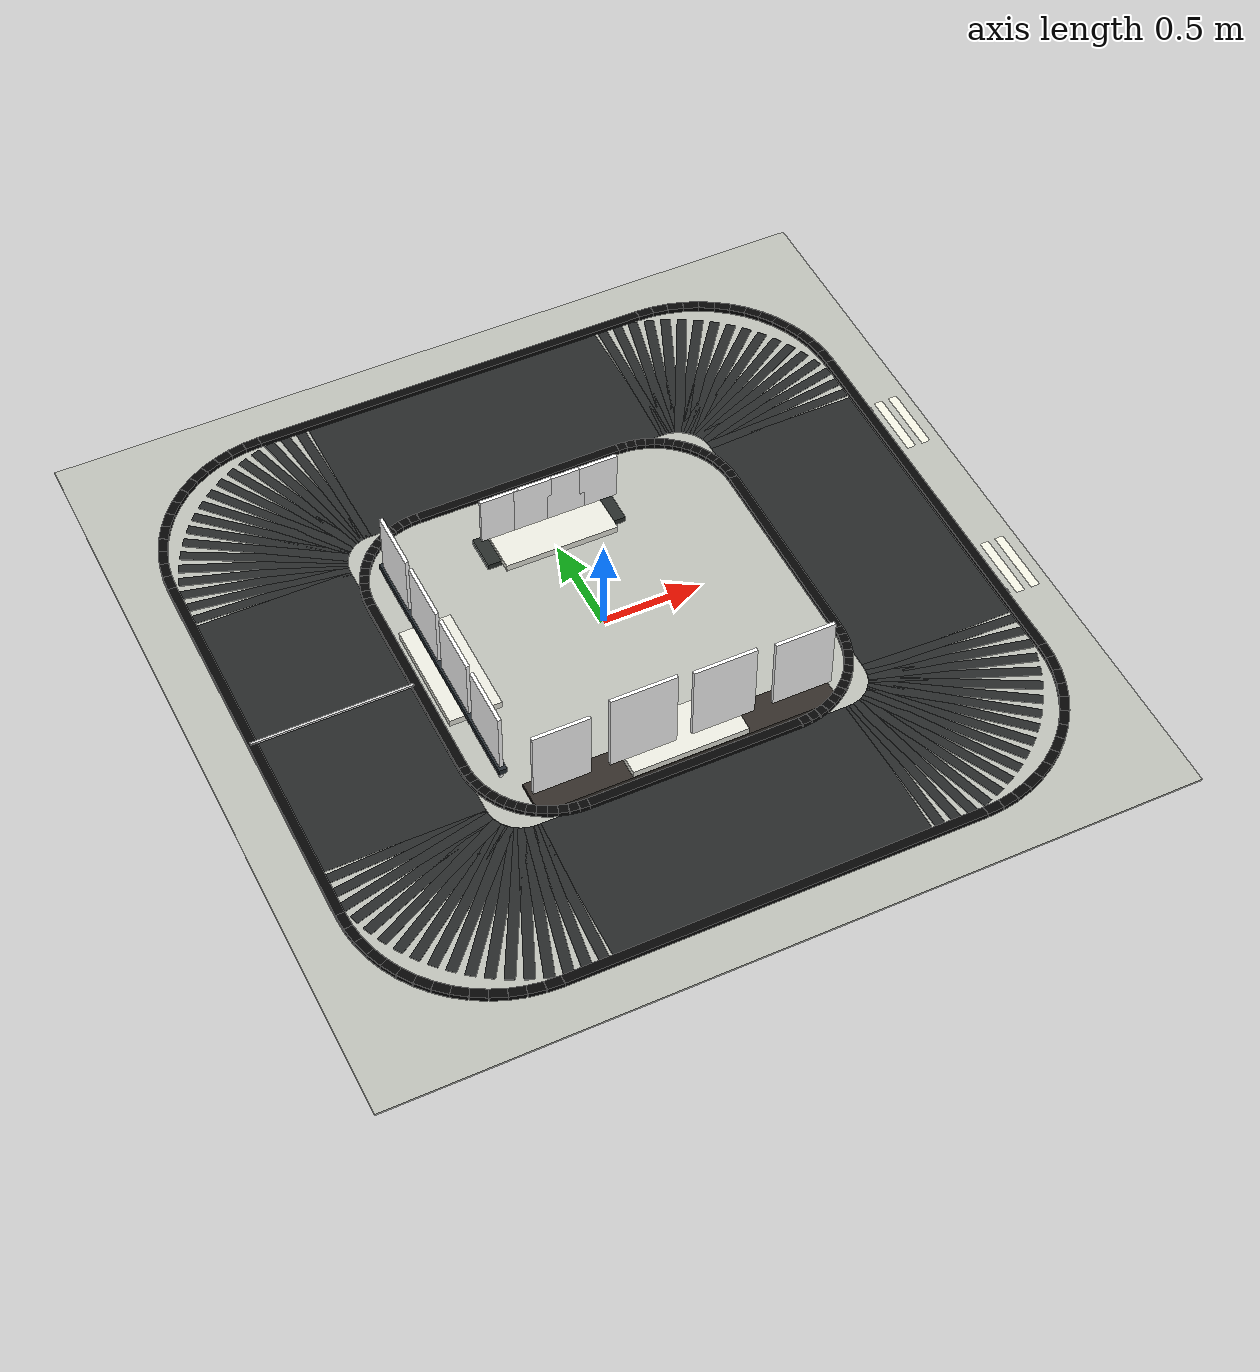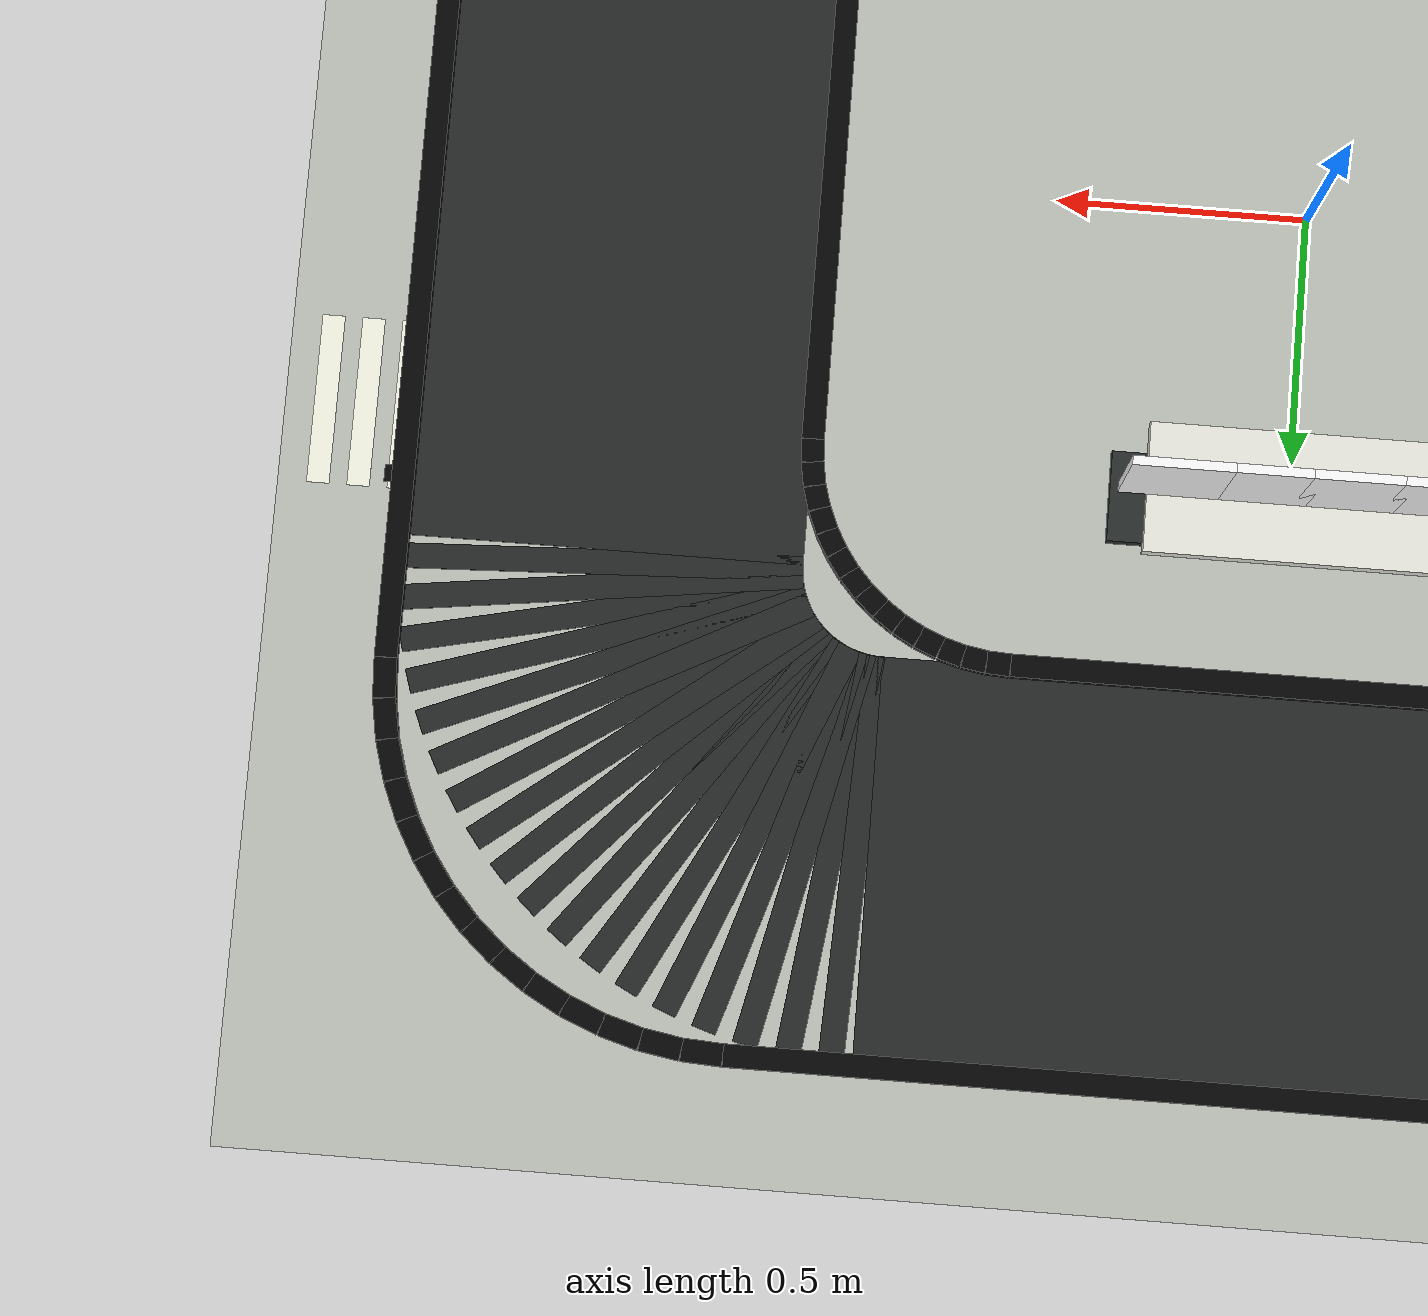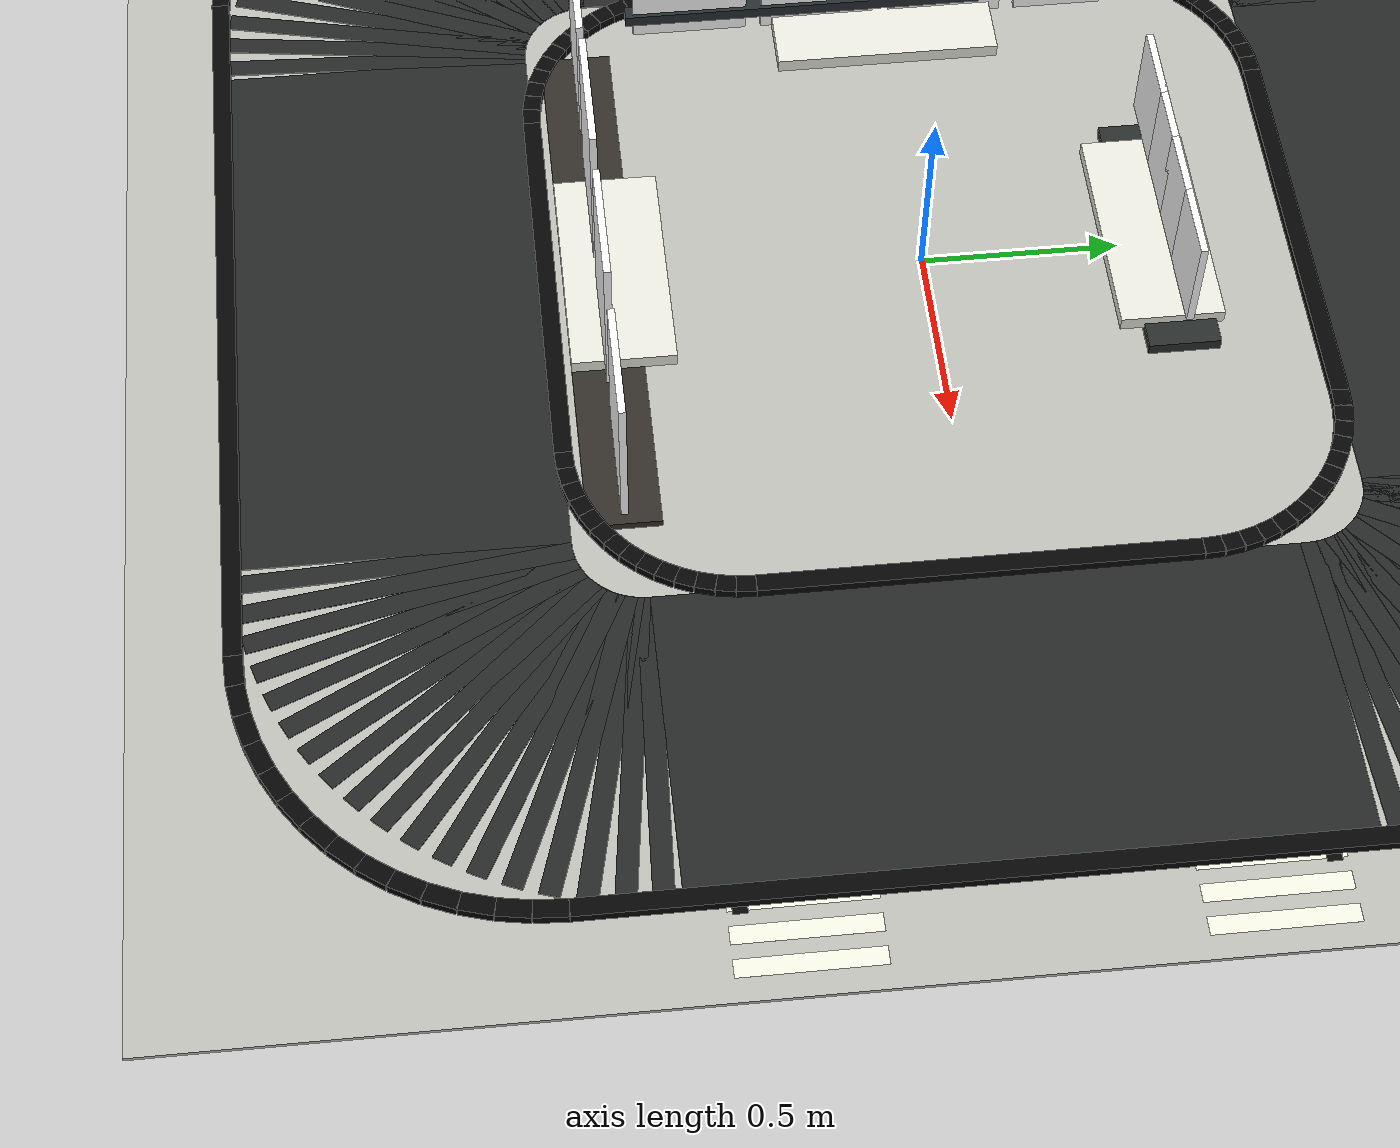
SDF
<sdf version="1.9">
 <world name="safe_city">
  <gravity>0 0 -9.8</gravity>
  <plugin filename="gz-sim-physics-system" name="gz::sim::systems::Physics"/>
  <plugin filename="gz-sim-sensors-system" name="gz::sim::systems::Sensors">
   <render_engine>ogre2</render_engine>
  </plugin>
  <plugin filename="gz-sim-user-commands-system" name="gz::sim::systems::UserCommands"/>
  <plugin filename="gz-sim-scene-broadcaster-system" name="gz::sim::systems::SceneBroadcaster"/>
  <light type="directional" name="sun">
   <pose>0 0 10 0 0 0</pose>
   <diffuse>0.85 0.85 0.85 1</diffuse>
   <specular>0.25 0.25 0.25 1</specular>
   <direction>-0.4 0.2 -0.9</direction>
  </light>
  <model name="ground_plane_4m">
   <static>true</static>
   <pose>0 0 0.005 0 0 0</pose>
   <link name="link">
    <collision name="collision"><geometry><box><size>4 4 0.01</size></box></geometry></collision>
    <visual name="visual">
     <geometry><box><size>4 4 0.01</size></box></geometry>
     <material><ambient>0.74 0.75 0.72 1</ambient><diffuse>0.74 0.75 0.72 1</diffuse></material>
    </visual>
   </link>
  </model>
  <model name="road_surface_00">
   <static>true</static>
   <pose>-1.3489 -0.8048 0.0060 0 0 -1.52716</pose>
   <link name="link">
    <visual name="visual">
     <geometry><box><size>0.0497 0.8000 0.0120</size></box></geometry>
     <material><ambient>0.15 0.16 0.16 1</ambient><diffuse>0.15 0.16 0.16 1</diffuse></material>
    </visual>
   </link>
  </model>
  <model name="road_surface_01">
   <static>true</static>
   <pose>-1.3446 -0.8543 0.0060 0 0 -1.43990</pose>
   <link name="link">
    <visual name="visual">
     <geometry><box><size>0.0497 0.8000 0.0120</size></box></geometry>
     <material><ambient>0.15 0.16 0.16 1</ambient><diffuse>0.15 0.16 0.16 1</diffuse></material>
    </visual>
   </link>
  </model>
  <model name="road_surface_02">
   <static>true</static>
   <pose>-1.3360 -0.9033 0.0060 0 0 -1.35263</pose>
   <link name="link">
    <visual name="visual">
     <geometry><box><size>0.0497 0.8000 0.0120</size></box></geometry>
     <material><ambient>0.15 0.16 0.16 1</ambient><diffuse>0.15 0.16 0.16 1</diffuse></material>
    </visual>
   </link>
  </model>
  <model name="road_surface_03">
   <static>true</static>
   <pose>-1.3231 -0.9512 0.0060 0 0 -1.26536</pose>
   <link name="link">
    <visual name="visual">
     <geometry><box><size>0.0497 0.8000 0.0120</size></box></geometry>
     <material><ambient>0.15 0.16 0.16 1</ambient><diffuse>0.15 0.16 0.16 1</diffuse></material>
    </visual>
   </link>
  </model>
  <model name="road_surface_04">
   <static>true</static>
   <pose>-1.3061 -0.9979 0.0060 0 0 -1.17810</pose>
   <link name="link">
    <visual name="visual">
     <geometry><box><size>0.0497 0.8000 0.0120</size></box></geometry>
     <material><ambient>0.15 0.16 0.16 1</ambient><diffuse>0.15 0.16 0.16 1</diffuse></material>
    </visual>
   </link>
  </model>
  <model name="road_surface_05">
   <static>true</static>
   <pose>-1.2851 -1.0429 0.0060 0 0 -1.09083</pose>
   <link name="link">
    <visual name="visual">
     <geometry><box><size>0.0497 0.8000 0.0120</size></box></geometry>
     <material><ambient>0.15 0.16 0.16 1</ambient><diffuse>0.15 0.16 0.16 1</diffuse></material>
    </visual>
   </link>
  </model>
  <model name="road_surface_06">
   <static>true</static>
   <pose>-1.2603 -1.0860 0.0060 0 0 -1.00356</pose>
   <link name="link">
    <visual name="visual">
     <geometry><box><size>0.0497 0.8000 0.0120</size></box></geometry>
     <material><ambient>0.15 0.16 0.16 1</ambient><diffuse>0.15 0.16 0.16 1</diffuse></material>
    </visual>
   </link>
  </model>
  <model name="road_surface_07">
   <static>true</static>
   <pose>-1.2318 -1.1267 0.0060 0 0 -0.91630</pose>
   <link name="link">
    <visual name="visual">
     <geometry><box><size>0.0497 0.8000 0.0120</size></box></geometry>
     <material><ambient>0.15 0.16 0.16 1</ambient><diffuse>0.15 0.16 0.16 1</diffuse></material>
    </visual>
   </link>
  </model>
  <model name="road_surface_08">
   <static>true</static>
   <pose>-1.1998 -1.1647 0.0060 0 0 -0.82903</pose>
   <link name="link">
    <visual name="visual">
     <geometry><box><size>0.0497 0.8000 0.0120</size></box></geometry>
     <material><ambient>0.15 0.16 0.16 1</ambient><diffuse>0.15 0.16 0.16 1</diffuse></material>
    </visual>
   </link>
  </model>
  <model name="road_surface_09">
   <static>true</static>
   <pose>-1.1647 -1.1998 0.0060 0 0 -0.74176</pose>
   <link name="link">
    <visual name="visual">
     <geometry><box><size>0.0497 0.8000 0.0120</size></box></geometry>
     <material><ambient>0.15 0.16 0.16 1</ambient><diffuse>0.15 0.16 0.16 1</diffuse></material>
    </visual>
   </link>
  </model>
  <model name="road_surface_10">
   <static>true</static>
   <pose>-1.1267 -1.2318 0.0060 0 0 -0.65450</pose>
   <link name="link">
    <visual name="visual">
     <geometry><box><size>0.0497 0.8000 0.0120</size></box></geometry>
     <material><ambient>0.15 0.16 0.16 1</ambient><diffuse>0.15 0.16 0.16 1</diffuse></material>
    </visual>
   </link>
  </model>
  <model name="road_surface_11">
   <static>true</static>
   <pose>-1.0860 -1.2603 0.0060 0 0 -0.56723</pose>
   <link name="link">
    <visual name="visual">
     <geometry><box><size>0.0497 0.8000 0.0120</size></box></geometry>
     <material><ambient>0.15 0.16 0.16 1</ambient><diffuse>0.15 0.16 0.16 1</diffuse></material>
    </visual>
   </link>
  </model>
  <model name="road_surface_12">
   <static>true</static>
   <pose>-1.0429 -1.2851 0.0060 0 0 -0.47997</pose>
   <link name="link">
    <visual name="visual">
     <geometry><box><size>0.0497 0.8000 0.0120</size></box></geometry>
     <material><ambient>0.15 0.16 0.16 1</ambient><diffuse>0.15 0.16 0.16 1</diffuse></material>
    </visual>
   </link>
  </model>
  <model name="road_surface_13">
   <static>true</static>
   <pose>-0.9979 -1.3061 0.0060 0 0 -0.39270</pose>
   <link name="link">
    <visual name="visual">
     <geometry><box><size>0.0497 0.8000 0.0120</size></box></geometry>
     <material><ambient>0.15 0.16 0.16 1</ambient><diffuse>0.15 0.16 0.16 1</diffuse></material>
    </visual>
   </link>
  </model>
  <model name="road_surface_14">
   <static>true</static>
   <pose>-0.9512 -1.3231 0.0060 0 0 -0.30543</pose>
   <link name="link">
    <visual name="visual">
     <geometry><box><size>0.0497 0.8000 0.0120</size></box></geometry>
     <material><ambient>0.15 0.16 0.16 1</ambient><diffuse>0.15 0.16 0.16 1</diffuse></material>
    </visual>
   </link>
  </model>
  <model name="road_surface_15">
   <static>true</static>
   <pose>-0.9033 -1.3360 0.0060 0 0 -0.21817</pose>
   <link name="link">
    <visual name="visual">
     <geometry><box><size>0.0497 0.8000 0.0120</size></box></geometry>
     <material><ambient>0.15 0.16 0.16 1</ambient><diffuse>0.15 0.16 0.16 1</diffuse></material>
    </visual>
   </link>
  </model>
  <model name="road_surface_16">
   <static>true</static>
   <pose>-0.8543 -1.3446 0.0060 0 0 -0.13090</pose>
   <link name="link">
    <visual name="visual">
     <geometry><box><size>0.0497 0.8000 0.0120</size></box></geometry>
     <material><ambient>0.15 0.16 0.16 1</ambient><diffuse>0.15 0.16 0.16 1</diffuse></material>
    </visual>
   </link>
  </model>
  <model name="road_surface_17">
   <static>true</static>
   <pose>-0.8048 -1.3489 0.0060 0 0 -0.04363</pose>
   <link name="link">
    <visual name="visual">
     <geometry><box><size>0.0497 0.8000 0.0120</size></box></geometry>
     <material><ambient>0.15 0.16 0.16 1</ambient><diffuse>0.15 0.16 0.16 1</diffuse></material>
    </visual>
   </link>
  </model>
  <model name="road_surface_18">
   <static>true</static>
   <pose>-0.0000 -1.3500 0.0060 0 0 0.00000</pose>
   <link name="link">
    <visual name="visual">
     <geometry><box><size>1.5600 0.8000 0.0120</size></box></geometry>
     <material><ambient>0.15 0.16 0.16 1</ambient><diffuse>0.15 0.16 0.16 1</diffuse></material>
    </visual>
   </link>
  </model>
  <model name="road_surface_19">
   <static>true</static>
   <pose>0.8048 -1.3489 0.0060 0 0 0.04363</pose>
   <link name="link">
    <visual name="visual">
     <geometry><box><size>0.0497 0.8000 0.0120</size></box></geometry>
     <material><ambient>0.15 0.16 0.16 1</ambient><diffuse>0.15 0.16 0.16 1</diffuse></material>
    </visual>
   </link>
  </model>
  <model name="road_surface_20">
   <static>true</static>
   <pose>0.8543 -1.3446 0.0060 0 0 0.13090</pose>
   <link name="link">
    <visual name="visual">
     <geometry><box><size>0.0497 0.8000 0.0120</size></box></geometry>
     <material><ambient>0.15 0.16 0.16 1</ambient><diffuse>0.15 0.16 0.16 1</diffuse></material>
    </visual>
   </link>
  </model>
  <model name="road_surface_21">
   <static>true</static>
   <pose>0.9033 -1.3360 0.0060 0 0 0.21817</pose>
   <link name="link">
    <visual name="visual">
     <geometry><box><size>0.0497 0.8000 0.0120</size></box></geometry>
     <material><ambient>0.15 0.16 0.16 1</ambient><diffuse>0.15 0.16 0.16 1</diffuse></material>
    </visual>
   </link>
  </model>
  <model name="road_surface_22">
   <static>true</static>
   <pose>0.9512 -1.3231 0.0060 0 0 0.30543</pose>
   <link name="link">
    <visual name="visual">
     <geometry><box><size>0.0497 0.8000 0.0120</size></box></geometry>
     <material><ambient>0.15 0.16 0.16 1</ambient><diffuse>0.15 0.16 0.16 1</diffuse></material>
    </visual>
   </link>
  </model>
  <model name="road_surface_23">
   <static>true</static>
   <pose>0.9979 -1.3061 0.0060 0 0 0.39270</pose>
   <link name="link">
    <visual name="visual">
     <geometry><box><size>0.0497 0.8000 0.0120</size></box></geometry>
     <material><ambient>0.15 0.16 0.16 1</ambient><diffuse>0.15 0.16 0.16 1</diffuse></material>
    </visual>
   </link>
  </model>
  <model name="road_surface_24">
   <static>true</static>
   <pose>1.0429 -1.2851 0.0060 0 0 0.47997</pose>
   <link name="link">
    <visual name="visual">
     <geometry><box><size>0.0497 0.8000 0.0120</size></box></geometry>
     <material><ambient>0.15 0.16 0.16 1</ambient><diffuse>0.15 0.16 0.16 1</diffuse></material>
    </visual>
   </link>
  </model>
  <model name="road_surface_25">
   <static>true</static>
   <pose>1.0860 -1.2603 0.0060 0 0 0.56723</pose>
   <link name="link">
    <visual name="visual">
     <geometry><box><size>0.0497 0.8000 0.0120</size></box></geometry>
     <material><ambient>0.15 0.16 0.16 1</ambient><diffuse>0.15 0.16 0.16 1</diffuse></material>
    </visual>
   </link>
  </model>
  <model name="road_surface_26">
   <static>true</static>
   <pose>1.1267 -1.2318 0.0060 0 0 0.65450</pose>
   <link name="link">
    <visual name="visual">
     <geometry><box><size>0.0497 0.8000 0.0120</size></box></geometry>
     <material><ambient>0.15 0.16 0.16 1</ambient><diffuse>0.15 0.16 0.16 1</diffuse></material>
    </visual>
   </link>
  </model>
  <model name="road_surface_27">
   <static>true</static>
   <pose>1.1647 -1.1998 0.0060 0 0 0.74176</pose>
   <link name="link">
    <visual name="visual">
     <geometry><box><size>0.0497 0.8000 0.0120</size></box></geometry>
     <material><ambient>0.15 0.16 0.16 1</ambient><diffuse>0.15 0.16 0.16 1</diffuse></material>
    </visual>
   </link>
  </model>
  <model name="road_surface_28">
   <static>true</static>
   <pose>1.1998 -1.1647 0.0060 0 0 0.82903</pose>
   <link name="link">
    <visual name="visual">
     <geometry><box><size>0.0497 0.8000 0.0120</size></box></geometry>
     <material><ambient>0.15 0.16 0.16 1</ambient><diffuse>0.15 0.16 0.16 1</diffuse></material>
    </visual>
   </link>
  </model>
  <model name="road_surface_29">
   <static>true</static>
   <pose>1.2318 -1.1267 0.0060 0 0 0.91630</pose>
   <link name="link">
    <visual name="visual">
     <geometry><box><size>0.0497 0.8000 0.0120</size></box></geometry>
     <material><ambient>0.15 0.16 0.16 1</ambient><diffuse>0.15 0.16 0.16 1</diffuse></material>
    </visual>
   </link>
  </model>
  <model name="road_surface_30">
   <static>true</static>
   <pose>1.2603 -1.0860 0.0060 0 0 1.00356</pose>
   <link name="link">
    <visual name="visual">
     <geometry><box><size>0.0497 0.8000 0.0120</size></box></geometry>
     <material><ambient>0.15 0.16 0.16 1</ambient><diffuse>0.15 0.16 0.16 1</diffuse></material>
    </visual>
   </link>
  </model>
  <model name="road_surface_31">
   <static>true</static>
   <pose>1.2851 -1.0429 0.0060 0 0 1.09083</pose>
   <link name="link">
    <visual name="visual">
     <geometry><box><size>0.0497 0.8000 0.0120</size></box></geometry>
     <material><ambient>0.15 0.16 0.16 1</ambient><diffuse>0.15 0.16 0.16 1</diffuse></material>
    </visual>
   </link>
  </model>
  <model name="road_surface_32">
   <static>true</static>
   <pose>1.3061 -0.9979 0.0060 0 0 1.17810</pose>
   <link name="link">
    <visual name="visual">
     <geometry><box><size>0.0497 0.8000 0.0120</size></box></geometry>
     <material><ambient>0.15 0.16 0.16 1</ambient><diffuse>0.15 0.16 0.16 1</diffuse></material>
    </visual>
   </link>
  </model>
  <model name="road_surface_33">
   <static>true</static>
   <pose>1.3231 -0.9512 0.0060 0 0 1.26536</pose>
   <link name="link">
    <visual name="visual">
     <geometry><box><size>0.0497 0.8000 0.0120</size></box></geometry>
     <material><ambient>0.15 0.16 0.16 1</ambient><diffuse>0.15 0.16 0.16 1</diffuse></material>
    </visual>
   </link>
  </model>
  <model name="road_surface_34">
   <static>true</static>
   <pose>1.3360 -0.9033 0.0060 0 0 1.35263</pose>
   <link name="link">
    <visual name="visual">
     <geometry><box><size>0.0497 0.8000 0.0120</size></box></geometry>
     <material><ambient>0.15 0.16 0.16 1</ambient><diffuse>0.15 0.16 0.16 1</diffuse></material>
    </visual>
   </link>
  </model>
  <model name="road_surface_35">
   <static>true</static>
   <pose>1.3446 -0.8543 0.0060 0 0 1.43990</pose>
   <link name="link">
    <visual name="visual">
     <geometry><box><size>0.0497 0.8000 0.0120</size></box></geometry>
     <material><ambient>0.15 0.16 0.16 1</ambient><diffuse>0.15 0.16 0.16 1</diffuse></material>
    </visual>
   </link>
  </model>
  <model name="road_surface_36">
   <static>true</static>
   <pose>1.3489 -0.8048 0.0060 0 0 1.52716</pose>
   <link name="link">
    <visual name="visual">
     <geometry><box><size>0.0497 0.8000 0.0120</size></box></geometry>
     <material><ambient>0.15 0.16 0.16 1</ambient><diffuse>0.15 0.16 0.16 1</diffuse></material>
    </visual>
   </link>
  </model>
  <model name="road_surface_37">
   <static>true</static>
   <pose>1.3500 -0.0000 0.0060 0 0 1.57080</pose>
   <link name="link">
    <visual name="visual">
     <geometry><box><size>1.5600 0.8000 0.0120</size></box></geometry>
     <material><ambient>0.15 0.16 0.16 1</ambient><diffuse>0.15 0.16 0.16 1</diffuse></material>
    </visual>
   </link>
  </model>
  <model name="road_surface_38">
   <static>true</static>
   <pose>1.3489 0.8048 0.0060 0 0 1.61443</pose>
   <link name="link">
    <visual name="visual">
     <geometry><box><size>0.0497 0.8000 0.0120</size></box></geometry>
     <material><ambient>0.15 0.16 0.16 1</ambient><diffuse>0.15 0.16 0.16 1</diffuse></material>
    </visual>
   </link>
  </model>
  <model name="road_surface_39">
   <static>true</static>
   <pose>1.3446 0.8543 0.0060 0 0 1.70170</pose>
   <link name="link">
    <visual name="visual">
     <geometry><box><size>0.0497 0.8000 0.0120</size></box></geometry>
     <material><ambient>0.15 0.16 0.16 1</ambient><diffuse>0.15 0.16 0.16 1</diffuse></material>
    </visual>
   </link>
  </model>
  <model name="road_surface_40">
   <static>true</static>
   <pose>1.3360 0.9033 0.0060 0 0 1.78896</pose>
   <link name="link">
    <visual name="visual">
     <geometry><box><size>0.0497 0.8000 0.0120</size></box></geometry>
     <material><ambient>0.15 0.16 0.16 1</ambient><diffuse>0.15 0.16 0.16 1</diffuse></material>
    </visual>
   </link>
  </model>
  <model name="road_surface_41">
   <static>true</static>
   <pose>1.3231 0.9512 0.0060 0 0 1.87623</pose>
   <link name="link">
    <visual name="visual">
     <geometry><box><size>0.0497 0.8000 0.0120</size></box></geometry>
     <material><ambient>0.15 0.16 0.16 1</ambient><diffuse>0.15 0.16 0.16 1</diffuse></material>
    </visual>
   </link>
  </model>
  <model name="road_surface_42">
   <static>true</static>
   <pose>1.3061 0.9979 0.0060 0 0 1.96350</pose>
   <link name="link">
    <visual name="visual">
     <geometry><box><size>0.0497 0.8000 0.0120</size></box></geometry>
     <material><ambient>0.15 0.16 0.16 1</ambient><diffuse>0.15 0.16 0.16 1</diffuse></material>
    </visual>
   </link>
  </model>
  <model name="road_surface_43">
   <static>true</static>
   <pose>1.2851 1.0429 0.0060 0 0 2.05076</pose>
   <link name="link">
    <visual name="visual">
     <geometry><box><size>0.0497 0.8000 0.0120</size></box></geometry>
     <material><ambient>0.15 0.16 0.16 1</ambient><diffuse>0.15 0.16 0.16 1</diffuse></material>
    </visual>
   </link>
  </model>
  <model name="road_surface_44">
   <static>true</static>
   <pose>1.2603 1.0860 0.0060 0 0 2.13803</pose>
   <link name="link">
    <visual name="visual">
     <geometry><box><size>0.0497 0.8000 0.0120</size></box></geometry>
     <material><ambient>0.15 0.16 0.16 1</ambient><diffuse>0.15 0.16 0.16 1</diffuse></material>
    </visual>
   </link>
  </model>
  <model name="road_surface_45">
   <static>true</static>
   <pose>1.2318 1.1267 0.0060 0 0 2.22529</pose>
   <link name="link">
    <visual name="visual">
     <geometry><box><size>0.0497 0.8000 0.0120</size></box></geometry>
     <material><ambient>0.15 0.16 0.16 1</ambient><diffuse>0.15 0.16 0.16 1</diffuse></material>
    </visual>
   </link>
  </model>
  <model name="road_surface_46">
   <static>true</static>
   <pose>1.1998 1.1647 0.0060 0 0 2.31256</pose>
   <link name="link">
    <visual name="visual">
     <geometry><box><size>0.0497 0.8000 0.0120</size></box></geometry>
     <material><ambient>0.15 0.16 0.16 1</ambient><diffuse>0.15 0.16 0.16 1</diffuse></material>
    </visual>
   </link>
  </model>
  <model name="road_surface_47">
   <static>true</static>
   <pose>1.1647 1.1998 0.0060 0 0 2.39983</pose>
   <link name="link">
    <visual name="visual">
     <geometry><box><size>0.0497 0.8000 0.0120</size></box></geometry>
     <material><ambient>0.15 0.16 0.16 1</ambient><diffuse>0.15 0.16 0.16 1</diffuse></material>
    </visual>
   </link>
  </model>
  <model name="road_surface_48">
   <static>true</static>
   <pose>1.1267 1.2318 0.0060 0 0 2.48709</pose>
   <link name="link">
    <visual name="visual">
     <geometry><box><size>0.0497 0.8000 0.0120</size></box></geometry>
     <material><ambient>0.15 0.16 0.16 1</ambient><diffuse>0.15 0.16 0.16 1</diffuse></material>
    </visual>
   </link>
  </model>
  <model name="road_surface_49">
   <static>true</static>
   <pose>1.0860 1.2603 0.0060 0 0 2.57436</pose>
   <link name="link">
    <visual name="visual">
     <geometry><box><size>0.0497 0.8000 0.0120</size></box></geometry>
     <material><ambient>0.15 0.16 0.16 1</ambient><diffuse>0.15 0.16 0.16 1</diffuse></material>
    </visual>
   </link>
  </model>
  <model name="road_surface_50">
   <static>true</static>
   <pose>1.0429 1.2851 0.0060 0 0 2.66163</pose>
   <link name="link">
    <visual name="visual">
     <geometry><box><size>0.0497 0.8000 0.0120</size></box></geometry>
     <material><ambient>0.15 0.16 0.16 1</ambient><diffuse>0.15 0.16 0.16 1</diffuse></material>
    </visual>
   </link>
  </model>
  <model name="road_surface_51">
   <static>true</static>
   <pose>0.9979 1.3061 0.0060 0 0 2.74889</pose>
   <link name="link">
    <visual name="visual">
     <geometry><box><size>0.0497 0.8000 0.0120</size></box></geometry>
     <material><ambient>0.15 0.16 0.16 1</ambient><diffuse>0.15 0.16 0.16 1</diffuse></material>
    </visual>
   </link>
  </model>
  <model name="road_surface_52">
   <static>true</static>
   <pose>0.9512 1.3231 0.0060 0 0 2.83616</pose>
   <link name="link">
    <visual name="visual">
     <geometry><box><size>0.0497 0.8000 0.0120</size></box></geometry>
     <material><ambient>0.15 0.16 0.16 1</ambient><diffuse>0.15 0.16 0.16 1</diffuse></material>
    </visual>
   </link>
  </model>
  <model name="road_surface_53">
   <static>true</static>
   <pose>0.9033 1.3360 0.0060 0 0 2.92343</pose>
   <link name="link">
    <visual name="visual">
     <geometry><box><size>0.0497 0.8000 0.0120</size></box></geometry>
     <material><ambient>0.15 0.16 0.16 1</ambient><diffuse>0.15 0.16 0.16 1</diffuse></material>
    </visual>
   </link>
  </model>
  <model name="road_surface_54">
   <static>true</static>
   <pose>0.8543 1.3446 0.0060 0 0 3.01069</pose>
   <link name="link">
    <visual name="visual">
     <geometry><box><size>0.0497 0.8000 0.0120</size></box></geometry>
     <material><ambient>0.15 0.16 0.16 1</ambient><diffuse>0.15 0.16 0.16 1</diffuse></material>
    </visual>
   </link>
  </model>
  <model name="road_surface_55">
   <static>true</static>
   <pose>0.8048 1.3489 0.0060 0 0 3.09796</pose>
   <link name="link">
    <visual name="visual">
     <geometry><box><size>0.0497 0.8000 0.0120</size></box></geometry>
     <material><ambient>0.15 0.16 0.16 1</ambient><diffuse>0.15 0.16 0.16 1</diffuse></material>
    </visual>
   </link>
  </model>
  <model name="road_surface_56">
   <static>true</static>
   <pose>0.0000 1.3500 0.0060 0 0 3.14159</pose>
   <link name="link">
    <visual name="visual">
     <geometry><box><size>1.5600 0.8000 0.0120</size></box></geometry>
     <material><ambient>0.15 0.16 0.16 1</ambient><diffuse>0.15 0.16 0.16 1</diffuse></material>
    </visual>
   </link>
  </model>
  <model name="road_surface_57">
   <static>true</static>
   <pose>-0.8048 1.3489 0.0060 0 0 -3.09796</pose>
   <link name="link">
    <visual name="visual">
     <geometry><box><size>0.0497 0.8000 0.0120</size></box></geometry>
     <material><ambient>0.15 0.16 0.16 1</ambient><diffuse>0.15 0.16 0.16 1</diffuse></material>
    </visual>
   </link>
  </model>
  <model name="road_surface_58">
   <static>true</static>
   <pose>-0.8543 1.3446 0.0060 0 0 -3.01069</pose>
   <link name="link">
    <visual name="visual">
     <geometry><box><size>0.0497 0.8000 0.0120</size></box></geometry>
     <material><ambient>0.15 0.16 0.16 1</ambient><diffuse>0.15 0.16 0.16 1</diffuse></material>
    </visual>
   </link>
  </model>
  <model name="road_surface_59">
   <static>true</static>
   <pose>-0.9033 1.3360 0.0060 0 0 -2.92343</pose>
   <link name="link">
    <visual name="visual">
     <geometry><box><size>0.0497 0.8000 0.0120</size></box></geometry>
     <material><ambient>0.15 0.16 0.16 1</ambient><diffuse>0.15 0.16 0.16 1</diffuse></material>
    </visual>
   </link>
  </model>
  <model name="road_surface_60">
   <static>true</static>
   <pose>-0.9512 1.3231 0.0060 0 0 -2.83616</pose>
   <link name="link">
    <visual name="visual">
     <geometry><box><size>0.0497 0.8000 0.0120</size></box></geometry>
     <material><ambient>0.15 0.16 0.16 1</ambient><diffuse>0.15 0.16 0.16 1</diffuse></material>
    </visual>
   </link>
  </model>
  <model name="road_surface_61">
   <static>true</static>
   <pose>-0.9979 1.3061 0.0060 0 0 -2.74889</pose>
   <link name="link">
    <visual name="visual">
     <geometry><box><size>0.0497 0.8000 0.0120</size></box></geometry>
     <material><ambient>0.15 0.16 0.16 1</ambient><diffuse>0.15 0.16 0.16 1</diffuse></material>
    </visual>
   </link>
  </model>
  <model name="road_surface_62">
   <static>true</static>
   <pose>-1.0429 1.2851 0.0060 0 0 -2.66163</pose>
   <link name="link">
    <visual name="visual">
     <geometry><box><size>0.0497 0.8000 0.0120</size></box></geometry>
     <material><ambient>0.15 0.16 0.16 1</ambient><diffuse>0.15 0.16 0.16 1</diffuse></material>
    </visual>
   </link>
  </model>
  <model name="road_surface_63">
   <static>true</static>
   <pose>-1.0860 1.2603 0.0060 0 0 -2.57436</pose>
   <link name="link">
    <visual name="visual">
     <geometry><box><size>0.0497 0.8000 0.0120</size></box></geometry>
     <material><ambient>0.15 0.16 0.16 1</ambient><diffuse>0.15 0.16 0.16 1</diffuse></material>
    </visual>
   </link>
  </model>
  <model name="road_surface_64">
   <static>true</static>
   <pose>-1.1267 1.2318 0.0060 0 0 -2.48709</pose>
   <link name="link">
    <visual name="visual">
     <geometry><box><size>0.0497 0.8000 0.0120</size></box></geometry>
     <material><ambient>0.15 0.16 0.16 1</ambient><diffuse>0.15 0.16 0.16 1</diffuse></material>
    </visual>
   </link>
  </model>
  <model name="road_surface_65">
   <static>true</static>
   <pose>-1.1647 1.1998 0.0060 0 0 -2.39983</pose>
   <link name="link">
    <visual name="visual">
     <geometry><box><size>0.0497 0.8000 0.0120</size></box></geometry>
     <material><ambient>0.15 0.16 0.16 1</ambient><diffuse>0.15 0.16 0.16 1</diffuse></material>
    </visual>
   </link>
  </model>
  <model name="road_surface_66">
   <static>true</static>
   <pose>-1.1998 1.1647 0.0060 0 0 -2.31256</pose>
   <link name="link">
    <visual name="visual">
     <geometry><box><size>0.0497 0.8000 0.0120</size></box></geometry>
     <material><ambient>0.15 0.16 0.16 1</ambient><diffuse>0.15 0.16 0.16 1</diffuse></material>
    </visual>
   </link>
  </model>
  <model name="road_surface_67">
   <static>true</static>
   <pose>-1.2318 1.1267 0.0060 0 0 -2.22529</pose>
   <link name="link">
    <visual name="visual">
     <geometry><box><size>0.0497 0.8000 0.0120</size></box></geometry>
     <material><ambient>0.15 0.16 0.16 1</ambient><diffuse>0.15 0.16 0.16 1</diffuse></material>
    </visual>
   </link>
  </model>
  <model name="road_surface_68">
   <static>true</static>
   <pose>-1.2603 1.0860 0.0060 0 0 -2.13803</pose>
   <link name="link">
    <visual name="visual">
     <geometry><box><size>0.0497 0.8000 0.0120</size></box></geometry>
     <material><ambient>0.15 0.16 0.16 1</ambient><diffuse>0.15 0.16 0.16 1</diffuse></material>
    </visual>
   </link>
  </model>
  <model name="road_surface_69">
   <static>true</static>
   <pose>-1.2851 1.0429 0.0060 0 0 -2.05076</pose>
   <link name="link">
    <visual name="visual">
     <geometry><box><size>0.0497 0.8000 0.0120</size></box></geometry>
     <material><ambient>0.15 0.16 0.16 1</ambient><diffuse>0.15 0.16 0.16 1</diffuse></material>
    </visual>
   </link>
  </model>
  <model name="road_surface_70">
   <static>true</static>
   <pose>-1.3061 0.9979 0.0060 0 0 -1.96350</pose>
   <link name="link">
    <visual name="visual">
     <geometry><box><size>0.0497 0.8000 0.0120</size></box></geometry>
     <material><ambient>0.15 0.16 0.16 1</ambient><diffuse>0.15 0.16 0.16 1</diffuse></material>
    </visual>
   </link>
  </model>
  <model name="road_surface_71">
   <static>true</static>
   <pose>-1.3231 0.9512 0.0060 0 0 -1.87623</pose>
   <link name="link">
    <visual name="visual">
     <geometry><box><size>0.0497 0.8000 0.0120</size></box></geometry>
     <material><ambient>0.15 0.16 0.16 1</ambient><diffuse>0.15 0.16 0.16 1</diffuse></material>
    </visual>
   </link>
  </model>
  <model name="road_surface_72">
   <static>true</static>
   <pose>-1.3360 0.9033 0.0060 0 0 -1.78896</pose>
   <link name="link">
    <visual name="visual">
     <geometry><box><size>0.0497 0.8000 0.0120</size></box></geometry>
     <material><ambient>0.15 0.16 0.16 1</ambient><diffuse>0.15 0.16 0.16 1</diffuse></material>
    </visual>
   </link>
  </model>
  <model name="road_surface_73">
   <static>true</static>
   <pose>-1.3446 0.8543 0.0060 0 0 -1.70170</pose>
   <link name="link">
    <visual name="visual">
     <geometry><box><size>0.0497 0.8000 0.0120</size></box></geometry>
     <material><ambient>0.15 0.16 0.16 1</ambient><diffuse>0.15 0.16 0.16 1</diffuse></material>
    </visual>
   </link>
  </model>
  <model name="road_surface_74">
   <static>true</static>
   <pose>-1.3489 0.8048 0.0060 0 0 -1.61443</pose>
   <link name="link">
    <visual name="visual">
     <geometry><box><size>0.0497 0.8000 0.0120</size></box></geometry>
     <material><ambient>0.15 0.16 0.16 1</ambient><diffuse>0.15 0.16 0.16 1</diffuse></material>
    </visual>
   </link>
  </model>
  <model name="road_surface_75">
   <static>true</static>
   <pose>-1.3500 0.0000 0.0060 0 0 -1.57080</pose>
   <link name="link">
    <visual name="visual">
     <geometry><box><size>1.5600 0.8000 0.0120</size></box></geometry>
     <material><ambient>0.15 0.16 0.16 1</ambient><diffuse>0.15 0.16 0.16 1</diffuse></material>
    </visual>
   </link>
  </model>
  <model name="outer_black_line_00">
   <static>true</static>
   <pose>-1.7477 -1.0703 0.0175 0 0 -1.51470</pose>
   <link name="link">
    <collision name="collision"><geometry><box><size>0.0807 0.0450 0.0350</size></box></geometry></collision>
    <visual name="visual">
     <geometry><box><size>0.0807 0.0450 0.0350</size></box></geometry>
     <material><ambient>0.02 0.02 0.02 1</ambient><diffuse>0.02 0.02 0.02 1</diffuse></material>
    </visual>
   </link>
  </model>
  <model name="outer_black_line_01">
   <static>true</static>
   <pose>-1.7387 -1.1504 0.0175 0 0 -1.40250</pose>
   <link name="link">
    <collision name="collision"><geometry><box><size>0.0807 0.0450 0.0350</size></box></geometry></collision>
    <visual name="visual">
     <geometry><box><size>0.0807 0.0450 0.0350</size></box></geometry>
     <material><ambient>0.02 0.02 0.02 1</ambient><diffuse>0.02 0.02 0.02 1</diffuse></material>
    </visual>
   </link>
  </model>
  <model name="outer_black_line_02">
   <static>true</static>
   <pose>-1.7208 -1.2290 0.0175 0 0 -1.29030</pose>
   <link name="link">
    <collision name="collision"><geometry><box><size>0.0807 0.0450 0.0350</size></box></geometry></collision>
    <visual name="visual">
     <geometry><box><size>0.0807 0.0450 0.0350</size></box></geometry>
     <material><ambient>0.02 0.02 0.02 1</ambient><diffuse>0.02 0.02 0.02 1</diffuse></material>
    </visual>
   </link>
  </model>
  <model name="outer_black_line_03">
   <static>true</static>
   <pose>-1.6941 -1.3051 0.0175 0 0 -1.17810</pose>
   <link name="link">
    <collision name="collision"><geometry><box><size>0.0807 0.0450 0.0350</size></box></geometry></collision>
    <visual name="visual">
     <geometry><box><size>0.0807 0.0450 0.0350</size></box></geometry>
     <material><ambient>0.02 0.02 0.02 1</ambient><diffuse>0.02 0.02 0.02 1</diffuse></material>
    </visual>
   </link>
  </model>
  <model name="outer_black_line_04">
   <static>true</static>
   <pose>-1.6592 -1.3777 0.0175 0 0 -1.06590</pose>
   <link name="link">
    <collision name="collision"><geometry><box><size>0.0807 0.0450 0.0350</size></box></geometry></collision>
    <visual name="visual">
     <geometry><box><size>0.0807 0.0450 0.0350</size></box></geometry>
     <material><ambient>0.02 0.02 0.02 1</ambient><diffuse>0.02 0.02 0.02 1</diffuse></material>
    </visual>
   </link>
  </model>
  <model name="outer_black_line_05">
   <static>true</static>
   <pose>-1.6163 -1.4460 0.0175 0 0 -0.95370</pose>
   <link name="link">
    <collision name="collision"><geometry><box><size>0.0807 0.0450 0.0350</size></box></geometry></collision>
    <visual name="visual">
     <geometry><box><size>0.0807 0.0450 0.0350</size></box></geometry>
     <material><ambient>0.02 0.02 0.02 1</ambient><diffuse>0.02 0.02 0.02 1</diffuse></material>
    </visual>
   </link>
  </model>
  <model name="outer_black_line_06">
   <static>true</static>
   <pose>-1.5660 -1.5090 0.0175 0 0 -0.84150</pose>
   <link name="link">
    <collision name="collision"><geometry><box><size>0.0807 0.0450 0.0350</size></box></geometry></collision>
    <visual name="visual">
     <geometry><box><size>0.0807 0.0450 0.0350</size></box></geometry>
     <material><ambient>0.02 0.02 0.02 1</ambient><diffuse>0.02 0.02 0.02 1</diffuse></material>
    </visual>
   </link>
  </model>
  <model name="outer_black_line_07">
   <static>true</static>
   <pose>-1.5090 -1.5660 0.0175 0 0 -0.72930</pose>
   <link name="link">
    <collision name="collision"><geometry><box><size>0.0807 0.0450 0.0350</size></box></geometry></collision>
    <visual name="visual">
     <geometry><box><size>0.0807 0.0450 0.0350</size></box></geometry>
     <material><ambient>0.02 0.02 0.02 1</ambient><diffuse>0.02 0.02 0.02 1</diffuse></material>
    </visual>
   </link>
  </model>
  <model name="outer_black_line_08">
   <static>true</static>
   <pose>-1.4460 -1.6163 0.0175 0 0 -0.61710</pose>
   <link name="link">
    <collision name="collision"><geometry><box><size>0.0807 0.0450 0.0350</size></box></geometry></collision>
    <visual name="visual">
     <geometry><box><size>0.0807 0.0450 0.0350</size></box></geometry>
     <material><ambient>0.02 0.02 0.02 1</ambient><diffuse>0.02 0.02 0.02 1</diffuse></material>
    </visual>
   </link>
  </model>
  <model name="outer_black_line_09">
   <static>true</static>
   <pose>-1.3777 -1.6592 0.0175 0 0 -0.50490</pose>
   <link name="link">
    <collision name="collision"><geometry><box><size>0.0807 0.0450 0.0350</size></box></geometry></collision>
    <visual name="visual">
     <geometry><box><size>0.0807 0.0450 0.0350</size></box></geometry>
     <material><ambient>0.02 0.02 0.02 1</ambient><diffuse>0.02 0.02 0.02 1</diffuse></material>
    </visual>
   </link>
  </model>
  <model name="outer_black_line_10">
   <static>true</static>
   <pose>-1.3051 -1.6941 0.0175 0 0 -0.39270</pose>
   <link name="link">
    <collision name="collision"><geometry><box><size>0.0807 0.0450 0.0350</size></box></geometry></collision>
    <visual name="visual">
     <geometry><box><size>0.0807 0.0450 0.0350</size></box></geometry>
     <material><ambient>0.02 0.02 0.02 1</ambient><diffuse>0.02 0.02 0.02 1</diffuse></material>
    </visual>
   </link>
  </model>
  <model name="outer_black_line_11">
   <static>true</static>
   <pose>-1.2290 -1.7208 0.0175 0 0 -0.28050</pose>
   <link name="link">
    <collision name="collision"><geometry><box><size>0.0807 0.0450 0.0350</size></box></geometry></collision>
    <visual name="visual">
     <geometry><box><size>0.0807 0.0450 0.0350</size></box></geometry>
     <material><ambient>0.02 0.02 0.02 1</ambient><diffuse>0.02 0.02 0.02 1</diffuse></material>
    </visual>
   </link>
  </model>
  <model name="outer_black_line_12">
   <static>true</static>
   <pose>-1.1504 -1.7387 0.0175 0 0 -0.16830</pose>
   <link name="link">
    <collision name="collision"><geometry><box><size>0.0807 0.0450 0.0350</size></box></geometry></collision>
    <visual name="visual">
     <geometry><box><size>0.0807 0.0450 0.0350</size></box></geometry>
     <material><ambient>0.02 0.02 0.02 1</ambient><diffuse>0.02 0.02 0.02 1</diffuse></material>
    </visual>
   </link>
  </model>
  <model name="outer_black_line_13">
   <static>true</static>
   <pose>-1.0703 -1.7477 0.0175 0 0 -0.05610</pose>
   <link name="link">
    <collision name="collision"><geometry><box><size>0.0807 0.0450 0.0350</size></box></geometry></collision>
    <visual name="visual">
     <geometry><box><size>0.0807 0.0450 0.0350</size></box></geometry>
     <material><ambient>0.02 0.02 0.02 1</ambient><diffuse>0.02 0.02 0.02 1</diffuse></material>
    </visual>
   </link>
  </model>
  <model name="outer_black_line_14">
   <static>true</static>
   <pose>-0.0000 -1.7500 0.0175 0 0 0.00000</pose>
   <link name="link">
    <collision name="collision"><geometry><box><size>2.0600 0.0450 0.0350</size></box></geometry></collision>
    <visual name="visual">
     <geometry><box><size>2.0600 0.0450 0.0350</size></box></geometry>
     <material><ambient>0.02 0.02 0.02 1</ambient><diffuse>0.02 0.02 0.02 1</diffuse></material>
    </visual>
   </link>
  </model>
  <model name="outer_black_line_15">
   <static>true</static>
   <pose>1.0703 -1.7477 0.0175 0 0 0.05610</pose>
   <link name="link">
    <collision name="collision"><geometry><box><size>0.0807 0.0450 0.0350</size></box></geometry></collision>
    <visual name="visual">
     <geometry><box><size>0.0807 0.0450 0.0350</size></box></geometry>
     <material><ambient>0.02 0.02 0.02 1</ambient><diffuse>0.02 0.02 0.02 1</diffuse></material>
    </visual>
   </link>
  </model>
  <model name="outer_black_line_16">
   <static>true</static>
   <pose>1.1504 -1.7387 0.0175 0 0 0.16830</pose>
   <link name="link">
    <collision name="collision"><geometry><box><size>0.0807 0.0450 0.0350</size></box></geometry></collision>
    <visual name="visual">
     <geometry><box><size>0.0807 0.0450 0.0350</size></box></geometry>
     <material><ambient>0.02 0.02 0.02 1</ambient><diffuse>0.02 0.02 0.02 1</diffuse></material>
    </visual>
   </link>
  </model>
  <model name="outer_black_line_17">
   <static>true</static>
   <pose>1.2290 -1.7208 0.0175 0 0 0.28050</pose>
   <link name="link">
    <collision name="collision"><geometry><box><size>0.0807 0.0450 0.0350</size></box></geometry></collision>
    <visual name="visual">
     <geometry><box><size>0.0807 0.0450 0.0350</size></box></geometry>
     <material><ambient>0.02 0.02 0.02 1</ambient><diffuse>0.02 0.02 0.02 1</diffuse></material>
    </visual>
   </link>
  </model>
  <model name="outer_black_line_18">
   <static>true</static>
   <pose>1.3051 -1.6941 0.0175 0 0 0.39270</pose>
   <link name="link">
    <collision name="collision"><geometry><box><size>0.0807 0.0450 0.0350</size></box></geometry></collision>
    <visual name="visual">
     <geometry><box><size>0.0807 0.0450 0.0350</size></box></geometry>
     <material><ambient>0.02 0.02 0.02 1</ambient><diffuse>0.02 0.02 0.02 1</diffuse></material>
    </visual>
   </link>
  </model>
  <model name="outer_black_line_19">
   <static>true</static>
   <pose>1.3777 -1.6592 0.0175 0 0 0.50490</pose>
   <link name="link">
    <collision name="collision"><geometry><box><size>0.0807 0.0450 0.0350</size></box></geometry></collision>
    <visual name="visual">
     <geometry><box><size>0.0807 0.0450 0.0350</size></box></geometry>
     <material><ambient>0.02 0.02 0.02 1</ambient><diffuse>0.02 0.02 0.02 1</diffuse></material>
    </visual>
   </link>
  </model>
  <model name="outer_black_line_20">
   <static>true</static>
   <pose>1.4460 -1.6163 0.0175 0 0 0.61710</pose>
   <link name="link">
    <collision name="collision"><geometry><box><size>0.0807 0.0450 0.0350</size></box></geometry></collision>
    <visual name="visual">
     <geometry><box><size>0.0807 0.0450 0.0350</size></box></geometry>
     <material><ambient>0.02 0.02 0.02 1</ambient><diffuse>0.02 0.02 0.02 1</diffuse></material>
    </visual>
   </link>
  </model>
  <model name="outer_black_line_21">
   <static>true</static>
   <pose>1.5090 -1.5660 0.0175 0 0 0.72930</pose>
   <link name="link">
    <collision name="collision"><geometry><box><size>0.0807 0.0450 0.0350</size></box></geometry></collision>
    <visual name="visual">
     <geometry><box><size>0.0807 0.0450 0.0350</size></box></geometry>
     <material><ambient>0.02 0.02 0.02 1</ambient><diffuse>0.02 0.02 0.02 1</diffuse></material>
    </visual>
   </link>
  </model>
  <model name="outer_black_line_22">
   <static>true</static>
   <pose>1.5660 -1.5090 0.0175 0 0 0.84150</pose>
   <link name="link">
    <collision name="collision"><geometry><box><size>0.0807 0.0450 0.0350</size></box></geometry></collision>
    <visual name="visual">
     <geometry><box><size>0.0807 0.0450 0.0350</size></box></geometry>
     <material><ambient>0.02 0.02 0.02 1</ambient><diffuse>0.02 0.02 0.02 1</diffuse></material>
    </visual>
   </link>
  </model>
  <model name="outer_black_line_23">
   <static>true</static>
   <pose>1.6163 -1.4460 0.0175 0 0 0.95370</pose>
   <link name="link">
    <collision name="collision"><geometry><box><size>0.0807 0.0450 0.0350</size></box></geometry></collision>
    <visual name="visual">
     <geometry><box><size>0.0807 0.0450 0.0350</size></box></geometry>
     <material><ambient>0.02 0.02 0.02 1</ambient><diffuse>0.02 0.02 0.02 1</diffuse></material>
    </visual>
   </link>
  </model>
  <model name="outer_black_line_24">
   <static>true</static>
   <pose>1.6592 -1.3777 0.0175 0 0 1.06590</pose>
   <link name="link">
    <collision name="collision"><geometry><box><size>0.0807 0.0450 0.0350</size></box></geometry></collision>
    <visual name="visual">
     <geometry><box><size>0.0807 0.0450 0.0350</size></box></geometry>
     <material><ambient>0.02 0.02 0.02 1</ambient><diffuse>0.02 0.02 0.02 1</diffuse></material>
    </visual>
   </link>
  </model>
  <model name="outer_black_line_25">
   <static>true</static>
   <pose>1.6941 -1.3051 0.0175 0 0 1.17810</pose>
   <link name="link">
    <collision name="collision"><geometry><box><size>0.0807 0.0450 0.0350</size></box></geometry></collision>
    <visual name="visual">
     <geometry><box><size>0.0807 0.0450 0.0350</size></box></geometry>
     <material><ambient>0.02 0.02 0.02 1</ambient><diffuse>0.02 0.02 0.02 1</diffuse></material>
    </visual>
   </link>
  </model>
  <model name="outer_black_line_26">
   <static>true</static>
   <pose>1.7208 -1.2290 0.0175 0 0 1.29030</pose>
   <link name="link">
    <collision name="collision"><geometry><box><size>0.0807 0.0450 0.0350</size></box></geometry></collision>
    <visual name="visual">
     <geometry><box><size>0.0807 0.0450 0.0350</size></box></geometry>
     <material><ambient>0.02 0.02 0.02 1</ambient><diffuse>0.02 0.02 0.02 1</diffuse></material>
    </visual>
   </link>
  </model>
  <model name="outer_black_line_27">
   <static>true</static>
   <pose>1.7387 -1.1504 0.0175 0 0 1.40250</pose>
   <link name="link">
    <collision name="collision"><geometry><box><size>0.0807 0.0450 0.0350</size></box></geometry></collision>
    <visual name="visual">
     <geometry><box><size>0.0807 0.0450 0.0350</size></box></geometry>
     <material><ambient>0.02 0.02 0.02 1</ambient><diffuse>0.02 0.02 0.02 1</diffuse></material>
    </visual>
   </link>
  </model>
  <model name="outer_black_line_28">
   <static>true</static>
   <pose>1.7477 -1.0703 0.0175 0 0 1.51470</pose>
   <link name="link">
    <collision name="collision"><geometry><box><size>0.0807 0.0450 0.0350</size></box></geometry></collision>
    <visual name="visual">
     <geometry><box><size>0.0807 0.0450 0.0350</size></box></geometry>
     <material><ambient>0.02 0.02 0.02 1</ambient><diffuse>0.02 0.02 0.02 1</diffuse></material>
    </visual>
   </link>
  </model>
  <model name="outer_black_line_29">
   <static>true</static>
   <pose>1.7500 -0.0000 0.0175 0 0 1.57080</pose>
   <link name="link">
    <collision name="collision"><geometry><box><size>2.0600 0.0450 0.0350</size></box></geometry></collision>
    <visual name="visual">
     <geometry><box><size>2.0600 0.0450 0.0350</size></box></geometry>
     <material><ambient>0.02 0.02 0.02 1</ambient><diffuse>0.02 0.02 0.02 1</diffuse></material>
    </visual>
   </link>
  </model>
  <model name="outer_black_line_30">
   <static>true</static>
   <pose>1.7477 1.0703 0.0175 0 0 1.62690</pose>
   <link name="link">
    <collision name="collision"><geometry><box><size>0.0807 0.0450 0.0350</size></box></geometry></collision>
    <visual name="visual">
     <geometry><box><size>0.0807 0.0450 0.0350</size></box></geometry>
     <material><ambient>0.02 0.02 0.02 1</ambient><diffuse>0.02 0.02 0.02 1</diffuse></material>
    </visual>
   </link>
  </model>
  <model name="outer_black_line_31">
   <static>true</static>
   <pose>1.7387 1.1504 0.0175 0 0 1.73910</pose>
   <link name="link">
    <collision name="collision"><geometry><box><size>0.0807 0.0450 0.0350</size></box></geometry></collision>
    <visual name="visual">
     <geometry><box><size>0.0807 0.0450 0.0350</size></box></geometry>
     <material><ambient>0.02 0.02 0.02 1</ambient><diffuse>0.02 0.02 0.02 1</diffuse></material>
    </visual>
   </link>
  </model>
  <model name="outer_black_line_32">
   <static>true</static>
   <pose>1.7208 1.2290 0.0175 0 0 1.85130</pose>
   <link name="link">
    <collision name="collision"><geometry><box><size>0.0807 0.0450 0.0350</size></box></geometry></collision>
    <visual name="visual">
     <geometry><box><size>0.0807 0.0450 0.0350</size></box></geometry>
     <material><ambient>0.02 0.02 0.02 1</ambient><diffuse>0.02 0.02 0.02 1</diffuse></material>
    </visual>
   </link>
  </model>
  <model name="outer_black_line_33">
   <static>true</static>
   <pose>1.6941 1.3051 0.0175 0 0 1.96350</pose>
   <link name="link">
    <collision name="collision"><geometry><box><size>0.0807 0.0450 0.0350</size></box></geometry></collision>
    <visual name="visual">
     <geometry><box><size>0.0807 0.0450 0.0350</size></box></geometry>
     <material><ambient>0.02 0.02 0.02 1</ambient><diffuse>0.02 0.02 0.02 1</diffuse></material>
    </visual>
   </link>
  </model>
  <model name="outer_black_line_34">
   <static>true</static>
   <pose>1.6592 1.3777 0.0175 0 0 2.07570</pose>
   <link name="link">
    <collision name="collision"><geometry><box><size>0.0807 0.0450 0.0350</size></box></geometry></collision>
    <visual name="visual">
     <geometry><box><size>0.0807 0.0450 0.0350</size></box></geometry>
     <material><ambient>0.02 0.02 0.02 1</ambient><diffuse>0.02 0.02 0.02 1</diffuse></material>
    </visual>
   </link>
  </model>
  <model name="outer_black_line_35">
   <static>true</static>
   <pose>1.6163 1.4460 0.0175 0 0 2.18789</pose>
   <link name="link">
    <collision name="collision"><geometry><box><size>0.0807 0.0450 0.0350</size></box></geometry></collision>
    <visual name="visual">
     <geometry><box><size>0.0807 0.0450 0.0350</size></box></geometry>
     <material><ambient>0.02 0.02 0.02 1</ambient><diffuse>0.02 0.02 0.02 1</diffuse></material>
    </visual>
   </link>
  </model>
  <model name="outer_black_line_36">
   <static>true</static>
   <pose>1.5660 1.5090 0.0175 0 0 2.30009</pose>
   <link name="link">
    <collision name="collision"><geometry><box><size>0.0807 0.0450 0.0350</size></box></geometry></collision>
    <visual name="visual">
     <geometry><box><size>0.0807 0.0450 0.0350</size></box></geometry>
     <material><ambient>0.02 0.02 0.02 1</ambient><diffuse>0.02 0.02 0.02 1</diffuse></material>
    </visual>
   </link>
  </model>
  <model name="outer_black_line_37">
   <static>true</static>
   <pose>1.5090 1.5660 0.0175 0 0 2.41229</pose>
   <link name="link">
    <collision name="collision"><geometry><box><size>0.0807 0.0450 0.0350</size></box></geometry></collision>
    <visual name="visual">
     <geometry><box><size>0.0807 0.0450 0.0350</size></box></geometry>
     <material><ambient>0.02 0.02 0.02 1</ambient><diffuse>0.02 0.02 0.02 1</diffuse></material>
    </visual>
   </link>
  </model>
  <model name="outer_black_line_38">
   <static>true</static>
   <pose>1.4460 1.6163 0.0175 0 0 2.52449</pose>
   <link name="link">
    <collision name="collision"><geometry><box><size>0.0807 0.0450 0.0350</size></box></geometry></collision>
    <visual name="visual">
     <geometry><box><size>0.0807 0.0450 0.0350</size></box></geometry>
     <material><ambient>0.02 0.02 0.02 1</ambient><diffuse>0.02 0.02 0.02 1</diffuse></material>
    </visual>
   </link>
  </model>
  <model name="outer_black_line_39">
   <static>true</static>
   <pose>1.3777 1.6592 0.0175 0 0 2.63669</pose>
   <link name="link">
    <collision name="collision"><geometry><box><size>0.0807 0.0450 0.0350</size></box></geometry></collision>
    <visual name="visual">
     <geometry><box><size>0.0807 0.0450 0.0350</size></box></geometry>
     <material><ambient>0.02 0.02 0.02 1</ambient><diffuse>0.02 0.02 0.02 1</diffuse></material>
    </visual>
   </link>
  </model>
  <model name="outer_black_line_40">
   <static>true</static>
   <pose>1.3051 1.6941 0.0175 0 0 2.74889</pose>
   <link name="link">
    <collision name="collision"><geometry><box><size>0.0807 0.0450 0.0350</size></box></geometry></collision>
    <visual name="visual">
     <geometry><box><size>0.0807 0.0450 0.0350</size></box></geometry>
     <material><ambient>0.02 0.02 0.02 1</ambient><diffuse>0.02 0.02 0.02 1</diffuse></material>
    </visual>
   </link>
  </model>
  <model name="outer_black_line_41">
   <static>true</static>
   <pose>1.2290 1.7208 0.0175 0 0 2.86109</pose>
   <link name="link">
    <collision name="collision"><geometry><box><size>0.0807 0.0450 0.0350</size></box></geometry></collision>
    <visual name="visual">
     <geometry><box><size>0.0807 0.0450 0.0350</size></box></geometry>
     <material><ambient>0.02 0.02 0.02 1</ambient><diffuse>0.02 0.02 0.02 1</diffuse></material>
    </visual>
   </link>
  </model>
  <model name="outer_black_line_42">
   <static>true</static>
   <pose>1.1504 1.7387 0.0175 0 0 2.97329</pose>
   <link name="link">
    <collision name="collision"><geometry><box><size>0.0807 0.0450 0.0350</size></box></geometry></collision>
    <visual name="visual">
     <geometry><box><size>0.0807 0.0450 0.0350</size></box></geometry>
     <material><ambient>0.02 0.02 0.02 1</ambient><diffuse>0.02 0.02 0.02 1</diffuse></material>
    </visual>
   </link>
  </model>
  <model name="outer_black_line_43">
   <static>true</static>
   <pose>1.0703 1.7477 0.0175 0 0 3.08549</pose>
   <link name="link">
    <collision name="collision"><geometry><box><size>0.0807 0.0450 0.0350</size></box></geometry></collision>
    <visual name="visual">
     <geometry><box><size>0.0807 0.0450 0.0350</size></box></geometry>
     <material><ambient>0.02 0.02 0.02 1</ambient><diffuse>0.02 0.02 0.02 1</diffuse></material>
    </visual>
   </link>
  </model>
  <model name="outer_black_line_44">
   <static>true</static>
   <pose>0.0000 1.7500 0.0175 0 0 3.14159</pose>
   <link name="link">
    <collision name="collision"><geometry><box><size>2.0600 0.0450 0.0350</size></box></geometry></collision>
    <visual name="visual">
     <geometry><box><size>2.0600 0.0450 0.0350</size></box></geometry>
     <material><ambient>0.02 0.02 0.02 1</ambient><diffuse>0.02 0.02 0.02 1</diffuse></material>
    </visual>
   </link>
  </model>
  <model name="outer_black_line_45">
   <static>true</static>
   <pose>-1.0703 1.7477 0.0175 0 0 -3.08549</pose>
   <link name="link">
    <collision name="collision"><geometry><box><size>0.0807 0.0450 0.0350</size></box></geometry></collision>
    <visual name="visual">
     <geometry><box><size>0.0807 0.0450 0.0350</size></box></geometry>
     <material><ambient>0.02 0.02 0.02 1</ambient><diffuse>0.02 0.02 0.02 1</diffuse></material>
    </visual>
   </link>
  </model>
  <model name="outer_black_line_46">
   <static>true</static>
   <pose>-1.1504 1.7387 0.0175 0 0 -2.97329</pose>
   <link name="link">
    <collision name="collision"><geometry><box><size>0.0807 0.0450 0.0350</size></box></geometry></collision>
    <visual name="visual">
     <geometry><box><size>0.0807 0.0450 0.0350</size></box></geometry>
     <material><ambient>0.02 0.02 0.02 1</ambient><diffuse>0.02 0.02 0.02 1</diffuse></material>
    </visual>
   </link>
  </model>
  <model name="outer_black_line_47">
   <static>true</static>
   <pose>-1.2290 1.7208 0.0175 0 0 -2.86109</pose>
   <link name="link">
    <collision name="collision"><geometry><box><size>0.0807 0.0450 0.0350</size></box></geometry></collision>
    <visual name="visual">
     <geometry><box><size>0.0807 0.0450 0.0350</size></box></geometry>
     <material><ambient>0.02 0.02 0.02 1</ambient><diffuse>0.02 0.02 0.02 1</diffuse></material>
    </visual>
   </link>
  </model>
  <model name="outer_black_line_48">
   <static>true</static>
   <pose>-1.3051 1.6941 0.0175 0 0 -2.74889</pose>
   <link name="link">
    <collision name="collision"><geometry><box><size>0.0807 0.0450 0.0350</size></box></geometry></collision>
    <visual name="visual">
     <geometry><box><size>0.0807 0.0450 0.0350</size></box></geometry>
     <material><ambient>0.02 0.02 0.02 1</ambient><diffuse>0.02 0.02 0.02 1</diffuse></material>
    </visual>
   </link>
  </model>
  <model name="outer_black_line_49">
   <static>true</static>
   <pose>-1.3777 1.6592 0.0175 0 0 -2.63669</pose>
   <link name="link">
    <collision name="collision"><geometry><box><size>0.0807 0.0450 0.0350</size></box></geometry></collision>
    <visual name="visual">
     <geometry><box><size>0.0807 0.0450 0.0350</size></box></geometry>
     <material><ambient>0.02 0.02 0.02 1</ambient><diffuse>0.02 0.02 0.02 1</diffuse></material>
    </visual>
   </link>
  </model>
  <model name="outer_black_line_50">
   <static>true</static>
   <pose>-1.4460 1.6163 0.0175 0 0 -2.52449</pose>
   <link name="link">
    <collision name="collision"><geometry><box><size>0.0807 0.0450 0.0350</size></box></geometry></collision>
    <visual name="visual">
     <geometry><box><size>0.0807 0.0450 0.0350</size></box></geometry>
     <material><ambient>0.02 0.02 0.02 1</ambient><diffuse>0.02 0.02 0.02 1</diffuse></material>
    </visual>
   </link>
  </model>
  <model name="outer_black_line_51">
   <static>true</static>
   <pose>-1.5090 1.5660 0.0175 0 0 -2.41229</pose>
   <link name="link">
    <collision name="collision"><geometry><box><size>0.0807 0.0450 0.0350</size></box></geometry></collision>
    <visual name="visual">
     <geometry><box><size>0.0807 0.0450 0.0350</size></box></geometry>
     <material><ambient>0.02 0.02 0.02 1</ambient><diffuse>0.02 0.02 0.02 1</diffuse></material>
    </visual>
   </link>
  </model>
  <model name="outer_black_line_52">
   <static>true</static>
   <pose>-1.5660 1.5090 0.0175 0 0 -2.30009</pose>
   <link name="link">
    <collision name="collision"><geometry><box><size>0.0807 0.0450 0.0350</size></box></geometry></collision>
    <visual name="visual">
     <geometry><box><size>0.0807 0.0450 0.0350</size></box></geometry>
     <material><ambient>0.02 0.02 0.02 1</ambient><diffuse>0.02 0.02 0.02 1</diffuse></material>
    </visual>
   </link>
  </model>
  <model name="outer_black_line_53">
   <static>true</static>
   <pose>-1.6163 1.4460 0.0175 0 0 -2.18789</pose>
   <link name="link">
    <collision name="collision"><geometry><box><size>0.0807 0.0450 0.0350</size></box></geometry></collision>
    <visual name="visual">
     <geometry><box><size>0.0807 0.0450 0.0350</size></box></geometry>
     <material><ambient>0.02 0.02 0.02 1</ambient><diffuse>0.02 0.02 0.02 1</diffuse></material>
    </visual>
   </link>
  </model>
  <model name="outer_black_line_54">
   <static>true</static>
   <pose>-1.6592 1.3777 0.0175 0 0 -2.07570</pose>
   <link name="link">
    <collision name="collision"><geometry><box><size>0.0807 0.0450 0.0350</size></box></geometry></collision>
    <visual name="visual">
     <geometry><box><size>0.0807 0.0450 0.0350</size></box></geometry>
     <material><ambient>0.02 0.02 0.02 1</ambient><diffuse>0.02 0.02 0.02 1</diffuse></material>
    </visual>
   </link>
  </model>
  <model name="outer_black_line_55">
   <static>true</static>
   <pose>-1.6941 1.3051 0.0175 0 0 -1.96350</pose>
   <link name="link">
    <collision name="collision"><geometry><box><size>0.0807 0.0450 0.0350</size></box></geometry></collision>
    <visual name="visual">
     <geometry><box><size>0.0807 0.0450 0.0350</size></box></geometry>
     <material><ambient>0.02 0.02 0.02 1</ambient><diffuse>0.02 0.02 0.02 1</diffuse></material>
    </visual>
   </link>
  </model>
  <model name="outer_black_line_56">
   <static>true</static>
   <pose>-1.7208 1.2290 0.0175 0 0 -1.85130</pose>
   <link name="link">
    <collision name="collision"><geometry><box><size>0.0807 0.0450 0.0350</size></box></geometry></collision>
    <visual name="visual">
     <geometry><box><size>0.0807 0.0450 0.0350</size></box></geometry>
     <material><ambient>0.02 0.02 0.02 1</ambient><diffuse>0.02 0.02 0.02 1</diffuse></material>
    </visual>
   </link>
  </model>
  <model name="outer_black_line_57">
   <static>true</static>
   <pose>-1.7387 1.1504 0.0175 0 0 -1.73910</pose>
   <link name="link">
    <collision name="collision"><geometry><box><size>0.0807 0.0450 0.0350</size></box></geometry></collision>
    <visual name="visual">
     <geometry><box><size>0.0807 0.0450 0.0350</size></box></geometry>
     <material><ambient>0.02 0.02 0.02 1</ambient><diffuse>0.02 0.02 0.02 1</diffuse></material>
    </visual>
   </link>
  </model>
  <model name="outer_black_line_58">
   <static>true</static>
   <pose>-1.7477 1.0703 0.0175 0 0 -1.62690</pose>
   <link name="link">
    <collision name="collision"><geometry><box><size>0.0807 0.0450 0.0350</size></box></geometry></collision>
    <visual name="visual">
     <geometry><box><size>0.0807 0.0450 0.0350</size></box></geometry>
     <material><ambient>0.02 0.02 0.02 1</ambient><diffuse>0.02 0.02 0.02 1</diffuse></material>
    </visual>
   </link>
  </model>
  <model name="outer_black_line_59">
   <static>true</static>
   <pose>-1.7500 0.0000 0.0175 0 0 -1.57080</pose>
   <link name="link">
    <collision name="collision"><geometry><box><size>2.0600 0.0450 0.0350</size></box></geometry></collision>
    <visual name="visual">
     <geometry><box><size>2.0600 0.0450 0.0350</size></box></geometry>
     <material><ambient>0.02 0.02 0.02 1</ambient><diffuse>0.02 0.02 0.02 1</diffuse></material>
    </visual>
   </link>
  </model>
  <model name="inner_black_line_00">
   <static>true</static>
   <pose>-0.9487 -0.5535 0.0175 0 0 -1.51470</pose>
   <link name="link">
    <collision name="collision"><geometry><box><size>0.0471 0.0450 0.0350</size></box></geometry></collision>
    <visual name="visual">
     <geometry><box><size>0.0471 0.0450 0.0350</size></box></geometry>
     <material><ambient>0.02 0.02 0.02 1</ambient><diffuse>0.02 0.02 0.02 1</diffuse></material>
    </visual>
   </link>
  </model>
  <model name="inner_black_line_01">
   <static>true</static>
   <pose>-0.9434 -0.6002 0.0175 0 0 -1.40250</pose>
   <link name="link">
    <collision name="collision"><geometry><box><size>0.0471 0.0450 0.0350</size></box></geometry></collision>
    <visual name="visual">
     <geometry><box><size>0.0471 0.0450 0.0350</size></box></geometry>
     <material><ambient>0.02 0.02 0.02 1</ambient><diffuse>0.02 0.02 0.02 1</diffuse></material>
    </visual>
   </link>
  </model>
  <model name="inner_black_line_02">
   <static>true</static>
   <pose>-0.9330 -0.6461 0.0175 0 0 -1.29030</pose>
   <link name="link">
    <collision name="collision"><geometry><box><size>0.0471 0.0450 0.0350</size></box></geometry></collision>
    <visual name="visual">
     <geometry><box><size>0.0471 0.0450 0.0350</size></box></geometry>
     <material><ambient>0.02 0.02 0.02 1</ambient><diffuse>0.02 0.02 0.02 1</diffuse></material>
    </visual>
   </link>
  </model>
  <model name="inner_black_line_03">
   <static>true</static>
   <pose>-0.9174 -0.6905 0.0175 0 0 -1.17810</pose>
   <link name="link">
    <collision name="collision"><geometry><box><size>0.0471 0.0450 0.0350</size></box></geometry></collision>
    <visual name="visual">
     <geometry><box><size>0.0471 0.0450 0.0350</size></box></geometry>
     <material><ambient>0.02 0.02 0.02 1</ambient><diffuse>0.02 0.02 0.02 1</diffuse></material>
    </visual>
   </link>
  </model>
  <model name="inner_black_line_04">
   <static>true</static>
   <pose>-0.8970 -0.7328 0.0175 0 0 -1.06590</pose>
   <link name="link">
    <collision name="collision"><geometry><box><size>0.0471 0.0450 0.0350</size></box></geometry></collision>
    <visual name="visual">
     <geometry><box><size>0.0471 0.0450 0.0350</size></box></geometry>
     <material><ambient>0.02 0.02 0.02 1</ambient><diffuse>0.02 0.02 0.02 1</diffuse></material>
    </visual>
   </link>
  </model>
  <model name="inner_black_line_05">
   <static>true</static>
   <pose>-0.8720 -0.7727 0.0175 0 0 -0.95370</pose>
   <link name="link">
    <collision name="collision"><geometry><box><size>0.0471 0.0450 0.0350</size></box></geometry></collision>
    <visual name="visual">
     <geometry><box><size>0.0471 0.0450 0.0350</size></box></geometry>
     <material><ambient>0.02 0.02 0.02 1</ambient><diffuse>0.02 0.02 0.02 1</diffuse></material>
    </visual>
   </link>
  </model>
  <model name="inner_black_line_06">
   <static>true</static>
   <pose>-0.8427 -0.8094 0.0175 0 0 -0.84150</pose>
   <link name="link">
    <collision name="collision"><geometry><box><size>0.0471 0.0450 0.0350</size></box></geometry></collision>
    <visual name="visual">
     <geometry><box><size>0.0471 0.0450 0.0350</size></box></geometry>
     <material><ambient>0.02 0.02 0.02 1</ambient><diffuse>0.02 0.02 0.02 1</diffuse></material>
    </visual>
   </link>
  </model>
  <model name="inner_black_line_07">
   <static>true</static>
   <pose>-0.8094 -0.8427 0.0175 0 0 -0.72930</pose>
   <link name="link">
    <collision name="collision"><geometry><box><size>0.0471 0.0450 0.0350</size></box></geometry></collision>
    <visual name="visual">
     <geometry><box><size>0.0471 0.0450 0.0350</size></box></geometry>
     <material><ambient>0.02 0.02 0.02 1</ambient><diffuse>0.02 0.02 0.02 1</diffuse></material>
    </visual>
   </link>
  </model>
  <model name="inner_black_line_08">
   <static>true</static>
   <pose>-0.7727 -0.8720 0.0175 0 0 -0.61710</pose>
   <link name="link">
    <collision name="collision"><geometry><box><size>0.0471 0.0450 0.0350</size></box></geometry></collision>
    <visual name="visual">
     <geometry><box><size>0.0471 0.0450 0.0350</size></box></geometry>
     <material><ambient>0.02 0.02 0.02 1</ambient><diffuse>0.02 0.02 0.02 1</diffuse></material>
    </visual>
   </link>
  </model>
  <model name="inner_black_line_09">
   <static>true</static>
   <pose>-0.7328 -0.8970 0.0175 0 0 -0.50490</pose>
   <link name="link">
    <collision name="collision"><geometry><box><size>0.0471 0.0450 0.0350</size></box></geometry></collision>
    <visual name="visual">
     <geometry><box><size>0.0471 0.0450 0.0350</size></box></geometry>
     <material><ambient>0.02 0.02 0.02 1</ambient><diffuse>0.02 0.02 0.02 1</diffuse></material>
    </visual>
   </link>
  </model>
  <model name="inner_black_line_10">
   <static>true</static>
   <pose>-0.6905 -0.9174 0.0175 0 0 -0.39270</pose>
   <link name="link">
    <collision name="collision"><geometry><box><size>0.0471 0.0450 0.0350</size></box></geometry></collision>
    <visual name="visual">
     <geometry><box><size>0.0471 0.0450 0.0350</size></box></geometry>
     <material><ambient>0.02 0.02 0.02 1</ambient><diffuse>0.02 0.02 0.02 1</diffuse></material>
    </visual>
   </link>
  </model>
  <model name="inner_black_line_11">
   <static>true</static>
   <pose>-0.6461 -0.9330 0.0175 0 0 -0.28050</pose>
   <link name="link">
    <collision name="collision"><geometry><box><size>0.0471 0.0450 0.0350</size></box></geometry></collision>
    <visual name="visual">
     <geometry><box><size>0.0471 0.0450 0.0350</size></box></geometry>
     <material><ambient>0.02 0.02 0.02 1</ambient><diffuse>0.02 0.02 0.02 1</diffuse></material>
    </visual>
   </link>
  </model>
  <model name="inner_black_line_12">
   <static>true</static>
   <pose>-0.6002 -0.9434 0.0175 0 0 -0.16830</pose>
   <link name="link">
    <collision name="collision"><geometry><box><size>0.0471 0.0450 0.0350</size></box></geometry></collision>
    <visual name="visual">
     <geometry><box><size>0.0471 0.0450 0.0350</size></box></geometry>
     <material><ambient>0.02 0.02 0.02 1</ambient><diffuse>0.02 0.02 0.02 1</diffuse></material>
    </visual>
   </link>
  </model>
  <model name="inner_black_line_13">
   <static>true</static>
   <pose>-0.5535 -0.9487 0.0175 0 0 -0.05610</pose>
   <link name="link">
    <collision name="collision"><geometry><box><size>0.0471 0.0450 0.0350</size></box></geometry></collision>
    <visual name="visual">
     <geometry><box><size>0.0471 0.0450 0.0350</size></box></geometry>
     <material><ambient>0.02 0.02 0.02 1</ambient><diffuse>0.02 0.02 0.02 1</diffuse></material>
    </visual>
   </link>
  </model>
  <model name="inner_black_line_14">
   <static>true</static>
   <pose>-0.0000 -0.9500 0.0175 0 0 0.00000</pose>
   <link name="link">
    <collision name="collision"><geometry><box><size>1.0600 0.0450 0.0350</size></box></geometry></collision>
    <visual name="visual">
     <geometry><box><size>1.0600 0.0450 0.0350</size></box></geometry>
     <material><ambient>0.02 0.02 0.02 1</ambient><diffuse>0.02 0.02 0.02 1</diffuse></material>
    </visual>
   </link>
  </model>
  <model name="inner_black_line_15">
   <static>true</static>
   <pose>0.5535 -0.9487 0.0175 0 0 0.05610</pose>
   <link name="link">
    <collision name="collision"><geometry><box><size>0.0471 0.0450 0.0350</size></box></geometry></collision>
    <visual name="visual">
     <geometry><box><size>0.0471 0.0450 0.0350</size></box></geometry>
     <material><ambient>0.02 0.02 0.02 1</ambient><diffuse>0.02 0.02 0.02 1</diffuse></material>
    </visual>
   </link>
  </model>
  <model name="inner_black_line_16">
   <static>true</static>
   <pose>0.6002 -0.9434 0.0175 0 0 0.16830</pose>
   <link name="link">
    <collision name="collision"><geometry><box><size>0.0471 0.0450 0.0350</size></box></geometry></collision>
    <visual name="visual">
     <geometry><box><size>0.0471 0.0450 0.0350</size></box></geometry>
     <material><ambient>0.02 0.02 0.02 1</ambient><diffuse>0.02 0.02 0.02 1</diffuse></material>
    </visual>
   </link>
  </model>
  <model name="inner_black_line_17">
   <static>true</static>
   <pose>0.6461 -0.9330 0.0175 0 0 0.28050</pose>
   <link name="link">
    <collision name="collision"><geometry><box><size>0.0471 0.0450 0.0350</size></box></geometry></collision>
    <visual name="visual">
     <geometry><box><size>0.0471 0.0450 0.0350</size></box></geometry>
     <material><ambient>0.02 0.02 0.02 1</ambient><diffuse>0.02 0.02 0.02 1</diffuse></material>
    </visual>
   </link>
  </model>
  <model name="inner_black_line_18">
   <static>true</static>
   <pose>0.6905 -0.9174 0.0175 0 0 0.39270</pose>
   <link name="link">
    <collision name="collision"><geometry><box><size>0.0471 0.0450 0.0350</size></box></geometry></collision>
    <visual name="visual">
     <geometry><box><size>0.0471 0.0450 0.0350</size></box></geometry>
     <material><ambient>0.02 0.02 0.02 1</ambient><diffuse>0.02 0.02 0.02 1</diffuse></material>
    </visual>
   </link>
  </model>
  <model name="inner_black_line_19">
   <static>true</static>
   <pose>0.7328 -0.8970 0.0175 0 0 0.50490</pose>
   <link name="link">
    <collision name="collision"><geometry><box><size>0.0471 0.0450 0.0350</size></box></geometry></collision>
    <visual name="visual">
     <geometry><box><size>0.0471 0.0450 0.0350</size></box></geometry>
     <material><ambient>0.02 0.02 0.02 1</ambient><diffuse>0.02 0.02 0.02 1</diffuse></material>
    </visual>
   </link>
  </model>
  <model name="inner_black_line_20">
   <static>true</static>
   <pose>0.7727 -0.8720 0.0175 0 0 0.61710</pose>
   <link name="link">
    <collision name="collision"><geometry><box><size>0.0471 0.0450 0.0350</size></box></geometry></collision>
    <visual name="visual">
     <geometry><box><size>0.0471 0.0450 0.0350</size></box></geometry>
     <material><ambient>0.02 0.02 0.02 1</ambient><diffuse>0.02 0.02 0.02 1</diffuse></material>
    </visual>
   </link>
  </model>
  <model name="inner_black_line_21">
   <static>true</static>
   <pose>0.8094 -0.8427 0.0175 0 0 0.72930</pose>
   <link name="link">
    <collision name="collision"><geometry><box><size>0.0471 0.0450 0.0350</size></box></geometry></collision>
    <visual name="visual">
     <geometry><box><size>0.0471 0.0450 0.0350</size></box></geometry>
     <material><ambient>0.02 0.02 0.02 1</ambient><diffuse>0.02 0.02 0.02 1</diffuse></material>
    </visual>
   </link>
  </model>
  <model name="inner_black_line_22">
   <static>true</static>
   <pose>0.8427 -0.8094 0.0175 0 0 0.84150</pose>
   <link name="link">
    <collision name="collision"><geometry><box><size>0.0471 0.0450 0.0350</size></box></geometry></collision>
    <visual name="visual">
     <geometry><box><size>0.0471 0.0450 0.0350</size></box></geometry>
     <material><ambient>0.02 0.02 0.02 1</ambient><diffuse>0.02 0.02 0.02 1</diffuse></material>
    </visual>
   </link>
  </model>
  <model name="inner_black_line_23">
   <static>true</static>
   <pose>0.8720 -0.7727 0.0175 0 0 0.95370</pose>
   <link name="link">
    <collision name="collision"><geometry><box><size>0.0471 0.0450 0.0350</size></box></geometry></collision>
    <visual name="visual">
     <geometry><box><size>0.0471 0.0450 0.0350</size></box></geometry>
     <material><ambient>0.02 0.02 0.02 1</ambient><diffuse>0.02 0.02 0.02 1</diffuse></material>
    </visual>
   </link>
  </model>
  <model name="inner_black_line_24">
   <static>true</static>
   <pose>0.8970 -0.7328 0.0175 0 0 1.06590</pose>
   <link name="link">
    <collision name="collision"><geometry><box><size>0.0471 0.0450 0.0350</size></box></geometry></collision>
    <visual name="visual">
     <geometry><box><size>0.0471 0.0450 0.0350</size></box></geometry>
     <material><ambient>0.02 0.02 0.02 1</ambient><diffuse>0.02 0.02 0.02 1</diffuse></material>
    </visual>
   </link>
  </model>
  <model name="inner_black_line_25">
   <static>true</static>
   <pose>0.9174 -0.6905 0.0175 0 0 1.17810</pose>
   <link name="link">
    <collision name="collision"><geometry><box><size>0.0471 0.0450 0.0350</size></box></geometry></collision>
    <visual name="visual">
     <geometry><box><size>0.0471 0.0450 0.0350</size></box></geometry>
     <material><ambient>0.02 0.02 0.02 1</ambient><diffuse>0.02 0.02 0.02 1</diffuse></material>
    </visual>
   </link>
  </model>
  <model name="inner_black_line_26">
   <static>true</static>
   <pose>0.9330 -0.6461 0.0175 0 0 1.29030</pose>
   <link name="link">
    <collision name="collision"><geometry><box><size>0.0471 0.0450 0.0350</size></box></geometry></collision>
    <visual name="visual">
     <geometry><box><size>0.0471 0.0450 0.0350</size></box></geometry>
     <material><ambient>0.02 0.02 0.02 1</ambient><diffuse>0.02 0.02 0.02 1</diffuse></material>
    </visual>
   </link>
  </model>
  <model name="inner_black_line_27">
   <static>true</static>
   <pose>0.9434 -0.6002 0.0175 0 0 1.40250</pose>
   <link name="link">
    <collision name="collision"><geometry><box><size>0.0471 0.0450 0.0350</size></box></geometry></collision>
    <visual name="visual">
     <geometry><box><size>0.0471 0.0450 0.0350</size></box></geometry>
     <material><ambient>0.02 0.02 0.02 1</ambient><diffuse>0.02 0.02 0.02 1</diffuse></material>
    </visual>
   </link>
  </model>
  <model name="inner_black_line_28">
   <static>true</static>
   <pose>0.9487 -0.5535 0.0175 0 0 1.51470</pose>
   <link name="link">
    <collision name="collision"><geometry><box><size>0.0471 0.0450 0.0350</size></box></geometry></collision>
    <visual name="visual">
     <geometry><box><size>0.0471 0.0450 0.0350</size></box></geometry>
     <material><ambient>0.02 0.02 0.02 1</ambient><diffuse>0.02 0.02 0.02 1</diffuse></material>
    </visual>
   </link>
  </model>
  <model name="inner_black_line_29">
   <static>true</static>
   <pose>0.9500 -0.0000 0.0175 0 0 1.57080</pose>
   <link name="link">
    <collision name="collision"><geometry><box><size>1.0600 0.0450 0.0350</size></box></geometry></collision>
    <visual name="visual">
     <geometry><box><size>1.0600 0.0450 0.0350</size></box></geometry>
     <material><ambient>0.02 0.02 0.02 1</ambient><diffuse>0.02 0.02 0.02 1</diffuse></material>
    </visual>
   </link>
  </model>
  <model name="inner_black_line_30">
   <static>true</static>
   <pose>0.9487 0.5535 0.0175 0 0 1.62690</pose>
   <link name="link">
    <collision name="collision"><geometry><box><size>0.0471 0.0450 0.0350</size></box></geometry></collision>
    <visual name="visual">
     <geometry><box><size>0.0471 0.0450 0.0350</size></box></geometry>
     <material><ambient>0.02 0.02 0.02 1</ambient><diffuse>0.02 0.02 0.02 1</diffuse></material>
    </visual>
   </link>
  </model>
  <model name="inner_black_line_31">
   <static>true</static>
   <pose>0.9434 0.6002 0.0175 0 0 1.73910</pose>
   <link name="link">
    <collision name="collision"><geometry><box><size>0.0471 0.0450 0.0350</size></box></geometry></collision>
    <visual name="visual">
     <geometry><box><size>0.0471 0.0450 0.0350</size></box></geometry>
     <material><ambient>0.02 0.02 0.02 1</ambient><diffuse>0.02 0.02 0.02 1</diffuse></material>
    </visual>
   </link>
  </model>
  <model name="inner_black_line_32">
   <static>true</static>
   <pose>0.9330 0.6461 0.0175 0 0 1.85130</pose>
   <link name="link">
    <collision name="collision"><geometry><box><size>0.0471 0.0450 0.0350</size></box></geometry></collision>
    <visual name="visual">
     <geometry><box><size>0.0471 0.0450 0.0350</size></box></geometry>
     <material><ambient>0.02 0.02 0.02 1</ambient><diffuse>0.02 0.02 0.02 1</diffuse></material>
    </visual>
   </link>
  </model>
  <model name="inner_black_line_33">
   <static>true</static>
   <pose>0.9174 0.6905 0.0175 0 0 1.96350</pose>
   <link name="link">
    <collision name="collision"><geometry><box><size>0.0471 0.0450 0.0350</size></box></geometry></collision>
    <visual name="visual">
     <geometry><box><size>0.0471 0.0450 0.0350</size></box></geometry>
     <material><ambient>0.02 0.02 0.02 1</ambient><diffuse>0.02 0.02 0.02 1</diffuse></material>
    </visual>
   </link>
  </model>
  <model name="inner_black_line_34">
   <static>true</static>
   <pose>0.8970 0.7328 0.0175 0 0 2.07570</pose>
   <link name="link">
    <collision name="collision"><geometry><box><size>0.0471 0.0450 0.0350</size></box></geometry></collision>
    <visual name="visual">
     <geometry><box><size>0.0471 0.0450 0.0350</size></box></geometry>
     <material><ambient>0.02 0.02 0.02 1</ambient><diffuse>0.02 0.02 0.02 1</diffuse></material>
    </visual>
   </link>
  </model>
  <model name="inner_black_line_35">
   <static>true</static>
   <pose>0.8720 0.7727 0.0175 0 0 2.18789</pose>
   <link name="link">
    <collision name="collision"><geometry><box><size>0.0471 0.0450 0.0350</size></box></geometry></collision>
    <visual name="visual">
     <geometry><box><size>0.0471 0.0450 0.0350</size></box></geometry>
     <material><ambient>0.02 0.02 0.02 1</ambient><diffuse>0.02 0.02 0.02 1</diffuse></material>
    </visual>
   </link>
  </model>
  <model name="inner_black_line_36">
   <static>true</static>
   <pose>0.8427 0.8094 0.0175 0 0 2.30009</pose>
   <link name="link">
    <collision name="collision"><geometry><box><size>0.0471 0.0450 0.0350</size></box></geometry></collision>
    <visual name="visual">
     <geometry><box><size>0.0471 0.0450 0.0350</size></box></geometry>
     <material><ambient>0.02 0.02 0.02 1</ambient><diffuse>0.02 0.02 0.02 1</diffuse></material>
    </visual>
   </link>
  </model>
  <model name="inner_black_line_37">
   <static>true</static>
   <pose>0.8094 0.8427 0.0175 0 0 2.41229</pose>
   <link name="link">
    <collision name="collision"><geometry><box><size>0.0471 0.0450 0.0350</size></box></geometry></collision>
    <visual name="visual">
     <geometry><box><size>0.0471 0.0450 0.0350</size></box></geometry>
     <material><ambient>0.02 0.02 0.02 1</ambient><diffuse>0.02 0.02 0.02 1</diffuse></material>
    </visual>
   </link>
  </model>
  <model name="inner_black_line_38">
   <static>true</static>
   <pose>0.7727 0.8720 0.0175 0 0 2.52449</pose>
   <link name="link">
    <collision name="collision"><geometry><box><size>0.0471 0.0450 0.0350</size></box></geometry></collision>
    <visual name="visual">
     <geometry><box><size>0.0471 0.0450 0.0350</size></box></geometry>
     <material><ambient>0.02 0.02 0.02 1</ambient><diffuse>0.02 0.02 0.02 1</diffuse></material>
    </visual>
   </link>
  </model>
  <model name="inner_black_line_39">
   <static>true</static>
   <pose>0.7328 0.8970 0.0175 0 0 2.63669</pose>
   <link name="link">
    <collision name="collision"><geometry><box><size>0.0471 0.0450 0.0350</size></box></geometry></collision>
    <visual name="visual">
     <geometry><box><size>0.0471 0.0450 0.0350</size></box></geometry>
     <material><ambient>0.02 0.02 0.02 1</ambient><diffuse>0.02 0.02 0.02 1</diffuse></material>
    </visual>
   </link>
  </model>
  <model name="inner_black_line_40">
   <static>true</static>
   <pose>0.6905 0.9174 0.0175 0 0 2.74889</pose>
   <link name="link">
    <collision name="collision"><geometry><box><size>0.0471 0.0450 0.0350</size></box></geometry></collision>
    <visual name="visual">
     <geometry><box><size>0.0471 0.0450 0.0350</size></box></geometry>
     <material><ambient>0.02 0.02 0.02 1</ambient><diffuse>0.02 0.02 0.02 1</diffuse></material>
    </visual>
   </link>
  </model>
  <model name="inner_black_line_41">
   <static>true</static>
   <pose>0.6461 0.9330 0.0175 0 0 2.86109</pose>
   <link name="link">
    <collision name="collision"><geometry><box><size>0.0471 0.0450 0.0350</size></box></geometry></collision>
    <visual name="visual">
     <geometry><box><size>0.0471 0.0450 0.0350</size></box></geometry>
     <material><ambient>0.02 0.02 0.02 1</ambient><diffuse>0.02 0.02 0.02 1</diffuse></material>
    </visual>
   </link>
  </model>
  <model name="inner_black_line_42">
   <static>true</static>
   <pose>0.6002 0.9434 0.0175 0 0 2.97329</pose>
   <link name="link">
    <collision name="collision"><geometry><box><size>0.0471 0.0450 0.0350</size></box></geometry></collision>
    <visual name="visual">
     <geometry><box><size>0.0471 0.0450 0.0350</size></box></geometry>
     <material><ambient>0.02 0.02 0.02 1</ambient><diffuse>0.02 0.02 0.02 1</diffuse></material>
    </visual>
   </link>
  </model>
  <model name="inner_black_line_43">
   <static>true</static>
   <pose>0.5535 0.9487 0.0175 0 0 3.08549</pose>
   <link name="link">
    <collision name="collision"><geometry><box><size>0.0471 0.0450 0.0350</size></box></geometry></collision>
    <visual name="visual">
     <geometry><box><size>0.0471 0.0450 0.0350</size></box></geometry>
     <material><ambient>0.02 0.02 0.02 1</ambient><diffuse>0.02 0.02 0.02 1</diffuse></material>
    </visual>
   </link>
  </model>
  <model name="inner_black_line_44">
   <static>true</static>
   <pose>0.0000 0.9500 0.0175 0 0 3.14159</pose>
   <link name="link">
    <collision name="collision"><geometry><box><size>1.0600 0.0450 0.0350</size></box></geometry></collision>
    <visual name="visual">
     <geometry><box><size>1.0600 0.0450 0.0350</size></box></geometry>
     <material><ambient>0.02 0.02 0.02 1</ambient><diffuse>0.02 0.02 0.02 1</diffuse></material>
    </visual>
   </link>
  </model>
  <model name="inner_black_line_45">
   <static>true</static>
   <pose>-0.5535 0.9487 0.0175 0 0 -3.08549</pose>
   <link name="link">
    <collision name="collision"><geometry><box><size>0.0471 0.0450 0.0350</size></box></geometry></collision>
    <visual name="visual">
     <geometry><box><size>0.0471 0.0450 0.0350</size></box></geometry>
     <material><ambient>0.02 0.02 0.02 1</ambient><diffuse>0.02 0.02 0.02 1</diffuse></material>
    </visual>
   </link>
  </model>
  <model name="inner_black_line_46">
   <static>true</static>
   <pose>-0.6002 0.9434 0.0175 0 0 -2.97329</pose>
   <link name="link">
    <collision name="collision"><geometry><box><size>0.0471 0.0450 0.0350</size></box></geometry></collision>
    <visual name="visual">
     <geometry><box><size>0.0471 0.0450 0.0350</size></box></geometry>
     <material><ambient>0.02 0.02 0.02 1</ambient><diffuse>0.02 0.02 0.02 1</diffuse></material>
    </visual>
   </link>
  </model>
  <model name="inner_black_line_47">
   <static>true</static>
   <pose>-0.6461 0.9330 0.0175 0 0 -2.86109</pose>
   <link name="link">
    <collision name="collision"><geometry><box><size>0.0471 0.0450 0.0350</size></box></geometry></collision>
    <visual name="visual">
     <geometry><box><size>0.0471 0.0450 0.0350</size></box></geometry>
     <material><ambient>0.02 0.02 0.02 1</ambient><diffuse>0.02 0.02 0.02 1</diffuse></material>
    </visual>
   </link>
  </model>
  <model name="inner_black_line_48">
   <static>true</static>
   <pose>-0.6905 0.9174 0.0175 0 0 -2.74889</pose>
   <link name="link">
    <collision name="collision"><geometry><box><size>0.0471 0.0450 0.0350</size></box></geometry></collision>
    <visual name="visual">
     <geometry><box><size>0.0471 0.0450 0.0350</size></box></geometry>
     <material><ambient>0.02 0.02 0.02 1</ambient><diffuse>0.02 0.02 0.02 1</diffuse></material>
    </visual>
   </link>
  </model>
  <model name="inner_black_line_49">
   <static>true</static>
   <pose>-0.7328 0.8970 0.0175 0 0 -2.63669</pose>
   <link name="link">
    <collision name="collision"><geometry><box><size>0.0471 0.0450 0.0350</size></box></geometry></collision>
    <visual name="visual">
     <geometry><box><size>0.0471 0.0450 0.0350</size></box></geometry>
     <material><ambient>0.02 0.02 0.02 1</ambient><diffuse>0.02 0.02 0.02 1</diffuse></material>
    </visual>
   </link>
  </model>
  <model name="inner_black_line_50">
   <static>true</static>
   <pose>-0.7727 0.8720 0.0175 0 0 -2.52449</pose>
   <link name="link">
    <collision name="collision"><geometry><box><size>0.0471 0.0450 0.0350</size></box></geometry></collision>
    <visual name="visual">
     <geometry><box><size>0.0471 0.0450 0.0350</size></box></geometry>
     <material><ambient>0.02 0.02 0.02 1</ambient><diffuse>0.02 0.02 0.02 1</diffuse></material>
    </visual>
   </link>
  </model>
  <model name="inner_black_line_51">
   <static>true</static>
   <pose>-0.8094 0.8427 0.0175 0 0 -2.41229</pose>
   <link name="link">
    <collision name="collision"><geometry><box><size>0.0471 0.0450 0.0350</size></box></geometry></collision>
    <visual name="visual">
     <geometry><box><size>0.0471 0.0450 0.0350</size></box></geometry>
     <material><ambient>0.02 0.02 0.02 1</ambient><diffuse>0.02 0.02 0.02 1</diffuse></material>
    </visual>
   </link>
  </model>
  <model name="inner_black_line_52">
   <static>true</static>
   <pose>-0.8427 0.8094 0.0175 0 0 -2.30009</pose>
   <link name="link">
    <collision name="collision"><geometry><box><size>0.0471 0.0450 0.0350</size></box></geometry></collision>
    <visual name="visual">
     <geometry><box><size>0.0471 0.0450 0.0350</size></box></geometry>
     <material><ambient>0.02 0.02 0.02 1</ambient><diffuse>0.02 0.02 0.02 1</diffuse></material>
    </visual>
   </link>
  </model>
  <model name="inner_black_line_53">
   <static>true</static>
   <pose>-0.8720 0.7727 0.0175 0 0 -2.18789</pose>
   <link name="link">
    <collision name="collision"><geometry><box><size>0.0471 0.0450 0.0350</size></box></geometry></collision>
    <visual name="visual">
     <geometry><box><size>0.0471 0.0450 0.0350</size></box></geometry>
     <material><ambient>0.02 0.02 0.02 1</ambient><diffuse>0.02 0.02 0.02 1</diffuse></material>
    </visual>
   </link>
  </model>
  <model name="inner_black_line_54">
   <static>true</static>
   <pose>-0.8970 0.7328 0.0175 0 0 -2.07570</pose>
   <link name="link">
    <collision name="collision"><geometry><box><size>0.0471 0.0450 0.0350</size></box></geometry></collision>
    <visual name="visual">
     <geometry><box><size>0.0471 0.0450 0.0350</size></box></geometry>
     <material><ambient>0.02 0.02 0.02 1</ambient><diffuse>0.02 0.02 0.02 1</diffuse></material>
    </visual>
   </link>
  </model>
  <model name="inner_black_line_55">
   <static>true</static>
   <pose>-0.9174 0.6905 0.0175 0 0 -1.96350</pose>
   <link name="link">
    <collision name="collision"><geometry><box><size>0.0471 0.0450 0.0350</size></box></geometry></collision>
    <visual name="visual">
     <geometry><box><size>0.0471 0.0450 0.0350</size></box></geometry>
     <material><ambient>0.02 0.02 0.02 1</ambient><diffuse>0.02 0.02 0.02 1</diffuse></material>
    </visual>
   </link>
  </model>
  <model name="inner_black_line_56">
   <static>true</static>
   <pose>-0.9330 0.6461 0.0175 0 0 -1.85130</pose>
   <link name="link">
    <collision name="collision"><geometry><box><size>0.0471 0.0450 0.0350</size></box></geometry></collision>
    <visual name="visual">
     <geometry><box><size>0.0471 0.0450 0.0350</size></box></geometry>
     <material><ambient>0.02 0.02 0.02 1</ambient><diffuse>0.02 0.02 0.02 1</diffuse></material>
    </visual>
   </link>
  </model>
  <model name="inner_black_line_57">
   <static>true</static>
   <pose>-0.9434 0.6002 0.0175 0 0 -1.73910</pose>
   <link name="link">
    <collision name="collision"><geometry><box><size>0.0471 0.0450 0.0350</size></box></geometry></collision>
    <visual name="visual">
     <geometry><box><size>0.0471 0.0450 0.0350</size></box></geometry>
     <material><ambient>0.02 0.02 0.02 1</ambient><diffuse>0.02 0.02 0.02 1</diffuse></material>
    </visual>
   </link>
  </model>
  <model name="inner_black_line_58">
   <static>true</static>
   <pose>-0.9487 0.5535 0.0175 0 0 -1.62690</pose>
   <link name="link">
    <collision name="collision"><geometry><box><size>0.0471 0.0450 0.0350</size></box></geometry></collision>
    <visual name="visual">
     <geometry><box><size>0.0471 0.0450 0.0350</size></box></geometry>
     <material><ambient>0.02 0.02 0.02 1</ambient><diffuse>0.02 0.02 0.02 1</diffuse></material>
    </visual>
   </link>
  </model>
  <model name="inner_black_line_59">
   <static>true</static>
   <pose>-0.9500 0.0000 0.0175 0 0 -1.57080</pose>
   <link name="link">
    <collision name="collision"><geometry><box><size>1.0600 0.0450 0.0350</size></box></geometry></collision>
    <visual name="visual">
     <geometry><box><size>1.0600 0.0450 0.0350</size></box></geometry>
     <material><ambient>0.02 0.02 0.02 1</ambient><diffuse>0.02 0.02 0.02 1</diffuse></material>
    </visual>
   </link>
  </model>
  <model name="left_800mm_dimension_line">
   <static>true</static>
   <pose>-1.36 0 0.035 0 0 0</pose>
   <link name="link">
    <visual name="visual">
     <geometry><box><size>0.80 0.012 0.012</size></box></geometry>
     <material><ambient>0.86 0.86 0.86 1</ambient><diffuse>0.86 0.86 0.86 1</diffuse></material>
    </visual>
   </link>
  </model>
  <model name="right_sidewalk_upper_line">
   <static>true</static>
   <pose>1.55 0.66 0.0116 0 0 0</pose>
   <link name="link">
    <visual name="visual">
     <geometry><plane><size>0.48 0.035</size></plane></geometry>
     <material><ambient>0.02 0.02 0.02 1</ambient><diffuse>0.02 0.02 0.02 1</diffuse></material>
    </visual>
   </link>
  </model>
  <model name="right_sidewalk_lower_line">
   <static>true</static>
   <pose>1.55 -0.66 0.0116 0 0 0</pose>
   <link name="link">
    <visual name="visual">
     <geometry><plane><size>0.48 0.035</size></plane></geometry>
     <material><ambient>0.02 0.02 0.02 1</ambient><diffuse>0.02 0.02 0.02 1</diffuse></material>
    </visual>
   </link>
  </model>
  <model name="right_crosswalk_upper_0">
   <static>true</static>
   <pose>1.520 0.520 0.0115 0 0 0</pose>
   <link name="link">
    <visual name="visual">
     <geometry><plane><size>0.045 0.34</size></plane></geometry>
     <material><ambient>0.96 0.96 0.90 1</ambient><diffuse>0.96 0.96 0.90 1</diffuse></material>
    </visual>
   </link>
  </model>
  <model name="right_crosswalk_upper_1">
   <static>true</static>
   <pose>1.600 0.520 0.0115 0 0 0</pose>
   <link name="link">
    <visual name="visual">
     <geometry><plane><size>0.045 0.34</size></plane></geometry>
     <material><ambient>0.96 0.96 0.90 1</ambient><diffuse>0.96 0.96 0.90 1</diffuse></material>
    </visual>
   </link>
  </model>
  <model name="right_crosswalk_upper_2">
   <static>true</static>
   <pose>1.680 0.520 0.0115 0 0 0</pose>
   <link name="link">
    <visual name="visual">
     <geometry><plane><size>0.045 0.34</size></plane></geometry>
     <material><ambient>0.96 0.96 0.90 1</ambient><diffuse>0.96 0.96 0.90 1</diffuse></material>
    </visual>
   </link>
  </model>
  <model name="right_crosswalk_upper_3">
   <static>true</static>
   <pose>1.760 0.520 0.0115 0 0 0</pose>
   <link name="link">
    <visual name="visual">
     <geometry><plane><size>0.045 0.34</size></plane></geometry>
     <material><ambient>0.96 0.96 0.90 1</ambient><diffuse>0.96 0.96 0.90 1</diffuse></material>
    </visual>
   </link>
  </model>
  <model name="right_crosswalk_upper_4">
   <static>true</static>
   <pose>1.840 0.520 0.0115 0 0 0</pose>
   <link name="link">
    <visual name="visual">
     <geometry><plane><size>0.045 0.34</size></plane></geometry>
     <material><ambient>0.96 0.96 0.90 1</ambient><diffuse>0.96 0.96 0.90 1</diffuse></material>
    </visual>
   </link>
  </model>
  <model name="right_crosswalk_upper_5">
   <static>true</static>
   <pose>1.920 0.520 0.0115 0 0 0</pose>
   <link name="link">
    <visual name="visual">
     <geometry><plane><size>0.045 0.34</size></plane></geometry>
     <material><ambient>0.96 0.96 0.90 1</ambient><diffuse>0.96 0.96 0.90 1</diffuse></material>
    </visual>
   </link>
  </model>
  <model name="right_crosswalk_lower_0">
   <static>true</static>
   <pose>1.520 -0.520 0.0115 0 0 0</pose>
   <link name="link">
    <visual name="visual">
     <geometry><plane><size>0.045 0.34</size></plane></geometry>
     <material><ambient>0.96 0.96 0.90 1</ambient><diffuse>0.96 0.96 0.90 1</diffuse></material>
    </visual>
   </link>
  </model>
  <model name="right_crosswalk_lower_1">
   <static>true</static>
   <pose>1.600 -0.520 0.0115 0 0 0</pose>
   <link name="link">
    <visual name="visual">
     <geometry><plane><size>0.045 0.34</size></plane></geometry>
     <material><ambient>0.96 0.96 0.90 1</ambient><diffuse>0.96 0.96 0.90 1</diffuse></material>
    </visual>
   </link>
  </model>
  <model name="right_crosswalk_lower_2">
   <static>true</static>
   <pose>1.680 -0.520 0.0115 0 0 0</pose>
   <link name="link">
    <visual name="visual">
     <geometry><plane><size>0.045 0.34</size></plane></geometry>
     <material><ambient>0.96 0.96 0.90 1</ambient><diffuse>0.96 0.96 0.90 1</diffuse></material>
    </visual>
   </link>
  </model>
  <model name="right_crosswalk_lower_3">
   <static>true</static>
   <pose>1.760 -0.520 0.0115 0 0 0</pose>
   <link name="link">
    <visual name="visual">
     <geometry><plane><size>0.045 0.34</size></plane></geometry>
     <material><ambient>0.96 0.96 0.90 1</ambient><diffuse>0.96 0.96 0.90 1</diffuse></material>
    </visual>
   </link>
  </model>
  <model name="right_crosswalk_lower_4">
   <static>true</static>
   <pose>1.840 -0.520 0.0115 0 0 0</pose>
   <link name="link">
    <visual name="visual">
     <geometry><plane><size>0.045 0.34</size></plane></geometry>
     <material><ambient>0.96 0.96 0.90 1</ambient><diffuse>0.96 0.96 0.90 1</diffuse></material>
    </visual>
   </link>
  </model>
  <model name="right_crosswalk_lower_5">
   <static>true</static>
   <pose>1.920 -0.520 0.0115 0 0 0</pose>
   <link name="link">
    <visual name="visual">
     <geometry><plane><size>0.045 0.34</size></plane></geometry>
     <material><ambient>0.96 0.96 0.90 1</ambient><diffuse>0.96 0.96 0.90 1</diffuse></material>
    </visual>
   </link>
  </model>
  <model name="trash_label_plate">
   <static>true</static>
   <pose>0 0.58 0.05 0 0 0</pose>
   <link name="link">
    <visual name="visual">
     <geometry><box><size>0.58 0.26 0.035</size></box></geometry>
     <material><ambient>0.92 0.92 0.88 1</ambient><diffuse>0.92 0.92 0.88 1</diffuse></material>
    </visual>
   </link>
  </model>
  <model name="trash_bin_models">
   <static>true</static>
   <pose>0 0.60 0.30 0 0 0</pose>
   <link name="link">
    <visual name="trash_real_photo_base">
     <pose>0 0 -0.270 0 0 0</pose>
     <geometry><box><size>0.72 0.18 0.030</size></box></geometry>
     <material><ambient>0.16 0.18 0.17 1</ambient><diffuse>0.16 0.18 0.17 1</diffuse></material>
    </visual>
    <visual name="kitchen_photo_billboard">
     <pose>-0.255 0 -0.04 0 0 0</pose>
     <geometry><box><size>0.195 0.018 0.260</size></box></geometry>
     <material>
      <ambient>1 1 1 1</ambient>
      <diffuse>1 1 1 1</diffuse>
      <pbr><metal><albedo_map>../materials/textures/kitchen_bin.jpg</albedo_map></metal></pbr>
     </material>
    </visual>
    <visual name="recyclable_photo_billboard">
     <pose>-0.085 0 -0.04 0 0 0</pose>
     <geometry><box><size>0.195 0.018 0.260</size></box></geometry>
     <material>
      <ambient>1 1 1 1</ambient>
      <diffuse>1 1 1 1</diffuse>
      <pbr><metal><albedo_map>../materials/textures/recyclable_bin.jpg</albedo_map></metal></pbr>
     </material>
    </visual>
    <visual name="hazardous_photo_billboard">
     <pose>0.085 0 -0.04 0 0 0</pose>
     <geometry><box><size>0.195 0.018 0.260</size></box></geometry>
     <material>
      <ambient>1 1 1 1</ambient>
      <diffuse>1 1 1 1</diffuse>
      <pbr><metal><albedo_map>../materials/textures/hazardous_bin.jpg</albedo_map></metal></pbr>
     </material>
    </visual>
    <visual name="other_photo_billboard">
     <pose>0.255 0 -0.04 0 0 0</pose>
     <geometry><box><size>0.195 0.018 0.260</size></box></geometry>
     <material>
      <ambient>1 1 1 1</ambient>
      <diffuse>1 1 1 1</diffuse>
      <pbr><metal><albedo_map>../materials/textures/other_bin.jpg</albedo_map></metal></pbr>
     </material>
    </visual>
   </link>
  </model>
  <model name="people_label_plate">
   <static>true</static>
   <pose>-0.78 0 0.05 0 0 1.5708</pose>
   <link name="link">
    <visual name="visual">
     <geometry><box><size>0.58 0.26 0.035</size></box></geometry>
     <material><ambient>0.92 0.92 0.88 1</ambient><diffuse>0.92 0.92 0.88 1</diffuse></material>
    </visual>
   </link>
  </model>
  <model name="people_models">
   <static>true</static>
   <pose>-0.82 0 0.32 0 0 0</pose>
   <link name="link">
    <visual name="people_real_photo_base">
     <pose>0 0 -0.220 0 0 0</pose>
     <geometry><box><size>0.040 1.36 0.030</size></box></geometry>
     <material><ambient>0.15 0.18 0.20 1</ambient><diffuse>0.15 0.18 0.20 1</diffuse></material>
    </visual>
    <visual name="medical_rescue_photo_billboard_a">
     <pose>0 -0.51 -0.08 0 0 0</pose>
     <geometry><box><size>0.018 0.300 0.400</size></box></geometry>
     <material>
      <ambient>1 1 1 1</ambient>
      <diffuse>1 1 1 1</diffuse>
      <pbr><metal><albedo_map>../materials/textures/medical_rescue_person_1.jpg</albedo_map></metal></pbr>
     </material>
    </visual>
    <visual name="normal_rescue_photo_billboard_a">
     <pose>0 -0.17 -0.08 0 0 0</pose>
     <geometry><box><size>0.018 0.300 0.400</size></box></geometry>
     <material>
      <ambient>1 1 1 1</ambient>
      <diffuse>1 1 1 1</diffuse>
      <pbr><metal><albedo_map>../materials/textures/normal_rescue_person_1.jpg</albedo_map></metal></pbr>
     </material>
    </visual>
    <visual name="medical_rescue_photo_billboard_b">
     <pose>0 0.17 -0.08 0 0 0</pose>
     <geometry><box><size>0.018 0.300 0.400</size></box></geometry>
     <material>
      <ambient>1 1 1 1</ambient>
      <diffuse>1 1 1 1</diffuse>
      <pbr><metal><albedo_map>../materials/textures/medical_rescue_person_2.jpg</albedo_map></metal></pbr>
     </material>
    </visual>
    <visual name="normal_rescue_photo_billboard_b">
     <pose>0 0.51 -0.08 0 0 0</pose>
     <geometry><box><size>0.018 0.300 0.400</size></box></geometry>
     <material>
      <ambient>1 1 1 1</ambient>
      <diffuse>1 1 1 1</diffuse>
      <pbr><metal><albedo_map>../materials/textures/normal_rescue_person_2.jpg</albedo_map></metal></pbr>
     </material>
    </visual>
   </link>
  </model>
  <model name="building_label_plate">
   <static>true</static>
   <pose>0 -0.78 0.05 0 0 0</pose>
   <link name="link">
    <visual name="visual">
     <geometry><box><size>0.58 0.26 0.035</size></box></geometry>
     <material><ambient>0.92 0.92 0.88 1</ambient><diffuse>0.92 0.92 0.88 1</diffuse></material>
    </visual>
   </link>
  </model>
  <model name="building_models">
   <static>true</static>
   <pose>0 -0.82 0.38 0 0 0</pose>
   <link name="link">
    <visual name="building_real_photo_base">
     <pose>0 0 -0.365 0 0 0</pose>
     <geometry><box><size>1.50 0.18 0.030</size></box></geometry>
     <material><ambient>0.20 0.18 0.16 1</ambient><diffuse>0.20 0.18 0.16 1</diffuse></material>
    </visual>
    <visual name="collapse_building_photo_billboard">
     <pose>-0.60 0 -0.12 0 0 0</pose>
     <geometry><box><size>0.285 0.018 0.380</size></box></geometry>
     <material>
      <ambient>1 1 1 1</ambient>
      <diffuse>1 1 1 1</diffuse>
      <pbr><metal><albedo_map>../materials/textures/collapse_building.jpg</albedo_map></metal></pbr>
     </material>
    </visual>
    <visual name="fire_building_photo_billboard">
     <pose>-0.20 0 -0.09 0 0 0</pose>
     <geometry><box><size>0.330 0.018 0.440</size></box></geometry>
     <material>
      <ambient>1 1 1 1</ambient>
      <diffuse>1 1 1 1</diffuse>
      <pbr><metal><albedo_map>../materials/textures/fire_building.jpg</albedo_map></metal></pbr>
     </material>
    </visual>
    <visual name="toxic_gas_building_photo_billboard">
     <pose>0.20 0 -0.10 0 0 0</pose>
     <geometry><box><size>0.315 0.018 0.420</size></box></geometry>
     <material>
      <ambient>1 1 1 1</ambient>
      <diffuse>1 1 1 1</diffuse>
      <pbr><metal><albedo_map>../materials/textures/toxic_gas_building.jpg</albedo_map></metal></pbr>
     </material>
    </visual>
    <visual name="power_failure_building_photo_billboard">
     <pose>0.60 0 -0.11 0 0 0</pose>
     <geometry><box><size>0.300 0.018 0.400</size></box></geometry>
     <material>
      <ambient>1 1 1 1</ambient>
      <diffuse>1 1 1 1</diffuse>
      <pbr><metal><albedo_map>../materials/textures/power_failure_building.jpg</albedo_map></metal></pbr>
     </material>
    </visual>
   </link>
  </model>
 </world>
</sdf>
